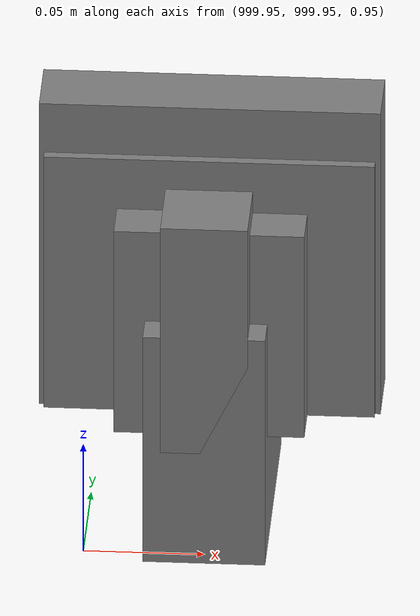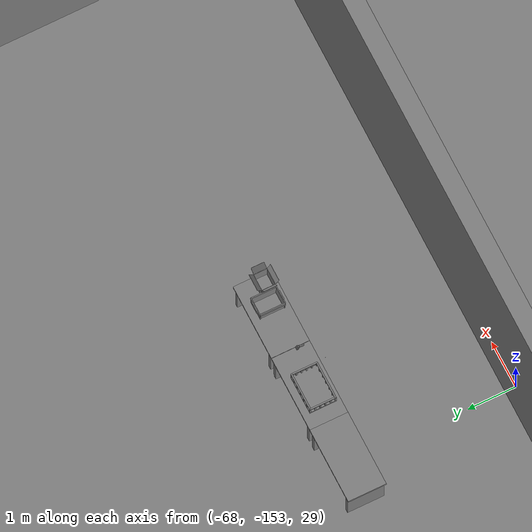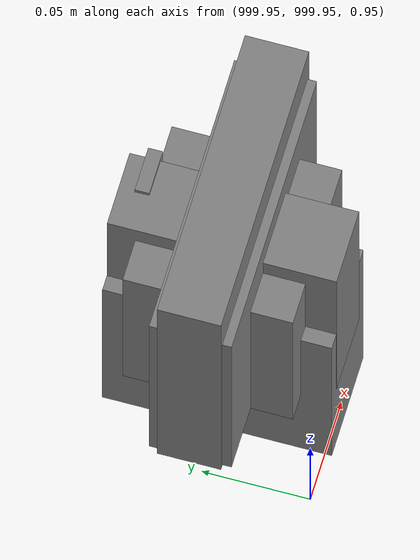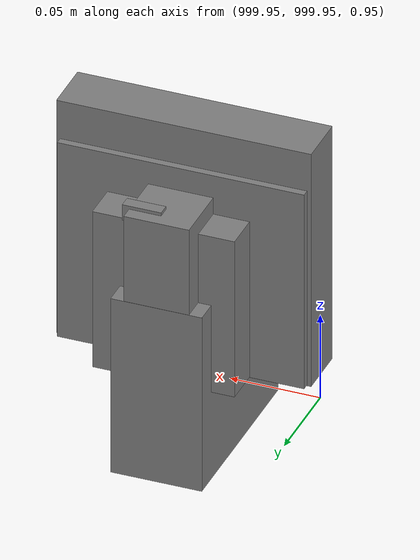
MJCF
<mujoco>
    <option gravity="0.000000000 0.000000000 -9.810000420" timestep="0.0049999999" integrator="implicitfast" density="1.225" viscosity="1.8000001e-05" noslip_iterations="10" iterations="100" sdf_iterations="50">
        <flag multiccd="disable"/>
    </option>
    <size memory="1000M"/>
    <compiler coordinate="local"/>
    <worldbody>
        <light cutoff="30" pos="0 1 1" dir="0 -1 -2"/>
        <light cutoff="30" pos="0 -1 1" dir="0 1 -2"/>
        <body pos="1000.000000000 1000.000000000 1.000000000" euler="0.000000000 0.000000000 180.000000000" name="openloong_gripper_2f85_fix_base_usda_cpu_fan">
            <geom contype="1" conaffinity="1" density="1000" type="box" material="" rgba="0.500000000 0.500000000 0.500000000 1.000000000" solimp="0.899999976 0.949999988 0.001000000" friction="1.000000000 0.005000000 0.000100000" solref="0.020000000 1.000000000" margin="0" condim="3" group="0" pos="0.000000000 0.000000000 0.070034981" quat="0.000000000 0.000000000 0.000000000 1.000000000" size="0.070700005 0.014699999 0.070700005" name="openloong_gripper_2f85_fix_base_usda_geom_734562B8_1CDB_4C23_80D8_C55B50CE7E51"/>
            <freejoint name="openloong_gripper_2f85_fix_base_usda_cpu_fan_joint"/>
            <site size="0.005000000 0.005000000 0.005000000" rgba="0.500000000 0.500000000 0.500000000 1.000000000" pos="0.000000000 0.000000000 0.000000000" quat="0.999961913 0.008726535 0.000000000 0.000000000" group="0" type="sphere" name="openloong_gripper_2f85_fix_base_usda_cpu_fancsite"/>
        </body>
        <body pos="-66.322074890 -149.413940430 31.163633347" euler="-98.901985168 -34.102039337 10.094217300" mocap="true" name="spotlight5_SpotLight"/>
        <body pos="1000.000000000 999.999938965 1.000000000" euler="0.000000000 0.000000000 180.000000000" name="openloong_gripper_2f85_fix_base_usda_intelcore_i5">
            <geom contype="1" conaffinity="1" density="1000" type="box" material="" rgba="0.500000000 0.500000000 0.500000000 1.000000000" solimp="0.899999976 0.949999988 0.001000000" friction="1.000000000 0.005000000 0.000100000" solref="0.020000000 1.000000000" margin="0" condim="3" group="0" pos="0.000000000 0.000000000 0.051722717" quat="0.707106709 0.000000000 0.000000000 -0.707106769" size="0.052800000 0.018080002 0.052800000" name="openloong_gripper_2f85_fix_base_usda_geom_59F1C608_60E0_45E0_86AE_DD2BB9E41B2C"/>
            <freejoint name="openloong_gripper_2f85_fix_base_usda_intelcore_i5_joint"/>
            <site size="0.005000000 0.005000000 0.005000000" rgba="0.500000000 0.500000000 0.500000000 1.000000000" pos="0.000000000 0.000000000 0.000000000" quat="0.999961913 0.008726534 0.000000000 0.000000000" group="0" type="sphere" name="openloong_gripper_2f85_fix_base_usda_intelcore_i5site"/>
        </body>
        <body pos="1000.000000000 1000.000000000 1.000000000" euler="0.000011953 0.000005123 -179.999984741" name="openloong_gripper_2f85_fix_base_usda_intel_box">
            <geom contype="1" conaffinity="1" density="1000" type="box" material="" rgba="0.500000000 0.500000000 0.500000000 1.000000000" solimp="0.899999976 0.949999988 0.001000000" friction="1.000000000 0.005000000 0.000100000" solref="0.020000000 1.000000000" margin="0" condim="3" group="0" pos="0.000000000 -0.000067139 0.000082284" quat="0.707106709 0.000000225 0.000000253 0.707106650" size="0.052800003 0.025300000 0.052800003" name="openloong_gripper_2f85_fix_base_usda_geom_DB704514_CA24_4BB3_9F83_FF99E2453BB3"/>
            <freejoint name="openloong_gripper_2f85_fix_base_usda_intel_box_joint"/>
            <site size="0.005000000 0.005000000 0.005000000" rgba="0.500000000 0.500000000 0.500000000 1.000000000" pos="0.000000000 0.000000000 0.000000000" quat="0.999961913 0.008726500 0.000000000 0.000000000" group="0" type="sphere" name="openloong_gripper_2f85_fix_base_usda_intel_boxsite"/>
        </body>
        <body pos="1000.000000000 1000.000000000 1.000000000" euler="0.000000000 0.000000000 180.000000000" name="openloong_gripper_2f85_fix_base_usda_wifi_box">
            <geom contype="1" conaffinity="1" density="1000" type="box" material="" rgba="0.500000000 0.500000000 0.500000000 1.000000000" solimp="0.899999976 0.949999988 0.001000000" friction="1.000000000 0.005000000 0.000100000" solref="0.020000000 1.000000000" margin="0" condim="3" group="0" pos="0.000000000 0.000000000 0.058978677" quat="0.000000000 0.000000047 0.000000000 1.000000000" size="0.068499997 0.018999999 0.059000000" name="openloong_gripper_2f85_fix_base_usda_geom_387782AB_372E_477B_A750_7B370F083870"/>
            <freejoint name="openloong_gripper_2f85_fix_base_usda_wifi_box_joint"/>
            <site size="0.005000000 0.005000000 0.005000000" rgba="0.500000000 0.500000000 0.500000000 1.000000000" pos="0.000000000 0.000000000 0.000000000" quat="0.999961913 0.008726500 0.000000000 0.000000000" group="0" type="sphere" name="openloong_gripper_2f85_fix_base_usda_wifi_boxsite"/>
        </body>
        <body pos="-66.002059937 -149.313888550 31.171628952" euler="34.022949219 -60.512500763 -49.154800415" mocap="true" name="spotlight3_SpotLight"/>
        <body pos="1000.000000000 1000.000000000 1.000000000" euler="0.000000000 0.000000000 180.000000000" name="openloong_gripper_2f85_fix_base_usda_battery_01">
            <geom contype="1" conaffinity="1" density="1000" type="box" material="" rgba="0.500000000 0.500000000 0.500000000 1.000000000" solimp="0.899999976 0.949999988 0.001000000" friction="1.000000000 0.005000000 0.000100000" solref="0.020000000 1.000000000" margin="0" condim="3" group="0" pos="-0.011123657 -0.041940309 0.101691343" quat="1.000000000 0.000000000 0.000000000 0.000000000" size="0.010800000 0.003375000 0.004725000" name="openloong_gripper_2f85_fix_base_usda_geom_BD21F07C_F330_4833_A9BA_980848E17CB0"/>
            <geom contype="1" conaffinity="1" density="1000" type="box" material="" rgba="0.500000000 0.500000000 0.500000000 1.000000000" solimp="0.899999976 0.949999988 0.001000000" friction="1.000000000 0.005000000 0.000100000" solref="0.020000000 1.000000000" margin="0" condim="3" group="0" pos="-0.010876465 -0.044247437 0.047066893" quat="0.998702705 -0.050920475 0.000000000 0.000000000" size="0.009450001 0.002700000 0.024975000" name="openloong_gripper_2f85_fix_base_usda_geom_D2077C25_C651_4948_A2C1_EAF4F04F0BEF"/>
            <geom contype="1" conaffinity="1" density="1000" type="box" material="" rgba="0.500000000 0.500000000 0.500000000 1.000000000" solimp="0.899999976 0.949999988 0.001000000" friction="1.000000000 0.005000000 0.000100000" solref="0.020000000 1.000000000" margin="0" condim="3" group="0" pos="-0.001235962 -0.000659180 0.047381196" quat="1.000000000 0.000000000 0.000000000 0.000000000" size="0.039420001 0.039150000 0.047250003" name="openloong_gripper_2f85_fix_base_usda_geom_8E34827E_7601_44B1_9C0C_90C50B8FBBE9"/>
            <geom contype="1" conaffinity="1" density="1000" type="box" material="" rgba="0.500000000 0.500000000 0.500000000 1.000000000" solimp="0.899999976 0.949999988 0.001000000" friction="1.000000000 0.005000000 0.000100000" solref="0.020000000 1.000000000" margin="0" condim="3" group="0" pos="-0.010876465 -0.039138794 0.009851727" quat="1.000000000 0.000000000 0.000000000 0.000000000" size="0.009450001 0.010800000 0.013500000" name="openloong_gripper_2f85_fix_base_usda_geom_11D423A2_D393_495D_A372_B4DFAA2F5A4E"/>
            <geom contype="1" conaffinity="1" density="1000" type="box" material="" rgba="0.500000000 0.500000000 0.500000000 1.000000000" solimp="0.899999976 0.949999988 0.001000000" friction="1.000000000 0.005000000 0.000100000" solref="0.020000000 1.000000000" margin="0" condim="3" group="0" pos="-0.010876465 -0.041528322 0.071508206" quat="1.000000000 0.000000000 0.000000000 0.000000000" size="0.009450001 0.002700000 0.027000001" name="openloong_gripper_2f85_fix_base_usda_geom_A5E3837A_8F86_4F47_8E25_DF6008C8651A"/>
            <freejoint name="openloong_gripper_2f85_fix_base_usda_battery_01_joint"/>
            <site size="0.005000000 0.005000000 0.005000000" rgba="0.500000000 0.500000000 0.500000000 1.000000000" pos="0.000000000 0.000000000 0.000000000" quat="0.999961913 0.008726500 0.000000000 0.000000000" group="0" type="sphere" name="openloong_gripper_2f85_fix_base_usda_battery_01site"/>
        </body>
        <body pos="-66.024734497 -148.913986206 31.170135498" euler="-14.872630119 60.042640686 -116.925918579" mocap="true" name="spotlight4_SpotLight"/>
        <body pos="-64.866622925 -149.383972168 30.183746338" euler="89.999984741 89.999946594 0.000000000" name="openloong_gripper_2f85_fix_base_usda_bluebox_01">
            <geom contype="1" conaffinity="1" density="1000" type="box" material="" rgba="0.500000000 0.500000000 0.500000000 1.000000000" solimp="0.899999976 0.949999988 0.001000000" friction="1.000000000 0.005000000 0.000100000" solref="0.020000000 1.000000000" margin="0" condim="3" group="0" pos="0.276580811 0.187225342 0.000068665" quat="0.707106948 0.000077471 0.707106352 0.000077486" size="0.100000001 0.057999998 0.010000000" name="openloong_gripper_2f85_fix_base_usda_geom_96AD08F8_4C6E_468C_9828_B6B1A17F58D4"/>
            <geom contype="1" conaffinity="1" density="1000" type="box" material="" rgba="0.500000000 0.500000000 0.500000000 1.000000000" solimp="0.899999976 0.949999988 0.001000000" friction="1.000000000 0.005000000 0.000100000" solref="0.020000000 1.000000000" margin="0" condim="3" group="0" pos="0.000000000 0.002883911 0.000000000" quat="0.999999881 0.000000000 0.000000000 0.000000000" size="0.254000008 0.003000000 0.172000006" name="openloong_gripper_2f85_fix_base_usda_geom_AA5CCEB0_55A9_4BF2_A5EF_F21D2348C6AC"/>
            <geom contype="1" conaffinity="1" density="1000" type="box" material="" rgba="0.500000000 0.500000000 0.500000000 1.000000000" solimp="0.899999976 0.949999988 0.001000000" friction="1.000000000 0.005000000 0.000100000" solref="0.020000000 1.000000000" margin="0" condim="3" group="0" pos="0.000000000 0.124874115 0.173484802" quat="0.999796331 0.020176515 -0.000000015 0.000000030" size="0.259999990 0.119999997 0.007000000" name="openloong_gripper_2f85_fix_base_usda_geom_91E173F9_C4B3_4BA2_A09E_50337E60E9A6"/>
            <geom contype="1" conaffinity="1" density="1000" type="box" material="" rgba="0.500000000 0.500000000 0.500000000 1.000000000" solimp="0.899999976 0.949999988 0.001000000" friction="1.000000000 0.005000000 0.000100000" solref="0.020000000 1.000000000" margin="0" condim="3" group="0" pos="0.000000000 0.124874115 -0.173469543" quat="0.999796331 -0.020176545 -0.000000015 0.000000000" size="0.259999990 0.119999997 0.007000000" name="openloong_gripper_2f85_fix_base_usda_geom_73BA2E66_E664_415B_99A9_8DEEF147C546"/>
            <geom contype="1" conaffinity="1" density="1000" type="box" material="" rgba="0.500000000 0.500000000 0.500000000 1.000000000" solimp="0.899999976 0.949999988 0.001000000" friction="1.000000000 0.005000000 0.000100000" solref="0.020000000 1.000000000" margin="0" condim="3" group="0" pos="0.000000000 0.214008331 0.188980103" quat="0.999912977 0.013176724 0.000000015 0.000000000" size="0.259999990 0.029999999 0.012500000" name="openloong_gripper_2f85_fix_base_usda_geom_521CCE80_35E2_443A_9D29_86AE5B84F514"/>
            <geom contype="1" conaffinity="1" density="1000" type="box" material="" rgba="0.500000000 0.500000000 0.500000000 1.000000000" solimp="0.899999976 0.949999988 0.001000000" friction="1.000000000 0.005000000 0.000100000" solref="0.020000000 1.000000000" margin="0" condim="3" group="0" pos="-0.258361816 0.125289917 0.001876831" quat="0.702796936 -0.020792112 0.710783124 0.020769298" size="0.189999998 0.119999997 0.009000000" name="openloong_gripper_2f85_fix_base_usda_geom_818BC29D_7B8E_4579_BFCD_09D331B849B2"/>
            <geom contype="1" conaffinity="1" density="1000" type="box" material="" rgba="0.500000000 0.500000000 0.500000000 1.000000000" solimp="0.899999976 0.949999988 0.001000000" friction="1.000000000 0.005000000 0.000100000" solref="0.020000000 1.000000000" margin="0" condim="3" group="0" pos="0.000000000 0.214008331 -0.188980103" quat="0.999912977 -0.013176769 0.000000030 0.000000015" size="0.259999990 0.029999999 0.012500000" name="openloong_gripper_2f85_fix_base_usda_geom_4AE4F4D7_2B8F_44E9_A269_E071F68E263C"/>
            <geom contype="1" conaffinity="1" density="1000" type="box" material="" rgba="0.500000000 0.500000000 0.500000000 1.000000000" solimp="0.899999976 0.949999988 0.001000000" friction="1.000000000 0.005000000 0.000100000" solref="0.020000000 1.000000000" margin="0" condim="3" group="0" pos="-0.276611328 0.187225342 0.000068665" quat="0.707106650 0.000077441 0.707106709 0.000077456" size="0.100000001 0.057999998 0.010000000" name="openloong_gripper_2f85_fix_base_usda_geom_58FBCBF1_9B04_42A2_BE6B_26F091FD1182"/>
            <geom contype="1" conaffinity="1" density="1000" type="box" material="" rgba="0.500000000 0.500000000 0.500000000 1.000000000" solimp="0.899999976 0.949999988 0.001000000" friction="1.000000000 0.005000000 0.000100000" solref="0.020000000 1.000000000" margin="0" condim="3" group="0" pos="0.258331299 0.125289917 0.001876831" quat="0.702851415 0.018856421 0.710823774 -0.019329369" size="0.189999998 0.119999997 0.009000000" name="openloong_gripper_2f85_fix_base_usda_geom_6D757CD4_A42A_4ED2_8631_75B2A3E89689"/>
            <freejoint name="openloong_gripper_2f85_fix_base_usda_bluebox_01_joint"/>
            <site size="0.005000000 0.005000000 0.005000000" rgba="0.500000000 0.500000000 0.500000000 1.000000000" pos="0.000000000 0.000000000 0.000000000" quat="0.999961913 0.008726534 0.000000000 0.000000000" group="0" type="sphere" name="openloong_gripper_2f85_fix_base_usda_bluebox_01site"/>
        </body>
        <body pos="-64.496299744 -149.491867065 30.235729218" euler="0.000000000 0.000000000 89.999946594" name="openloong_gripper_2f85_fix_base_usda_cardboardbox_01">
            <geom contype="1" conaffinity="1" density="1000" type="box" material="" rgba="0.500000000 0.500000000 0.500000000 1.000000000" solimp="0.899999976 0.949999988 0.001000000" friction="1.000000000 0.005000000 0.000100000" solref="0.020000000 1.000000000" margin="0" condim="3" group="0" pos="-0.003166199 -0.004086494 0.005052090" quat="1.000000000 0.000000000 0.000000000 0.000000000" size="0.142499998 0.177500010 0.005000000" name="openloong_gripper_2f85_fix_base_usda_geom_FF08E902_3156_44DB_A442_2709C8E16257"/>
            <geom contype="1" conaffinity="1" density="1000" type="box" material="" rgba="0.500000000 0.500000000 0.500000000 1.000000000" solimp="0.899999976 0.949999988 0.001000000" friction="1.000000000 0.005000000 0.000100000" solref="0.020000000 1.000000000" margin="0" condim="3" group="0" pos="-0.003166199 0.170316696 0.150570869" quat="1.000000000 0.000000000 0.000000000 0.000000000" size="0.142499998 0.005000000 0.149999991" name="openloong_gripper_2f85_fix_base_usda_geom_F5DF3E88_DD9F_4F52_B460_F1AB0E82F56A"/>
            <geom contype="1" conaffinity="1" density="1000" type="box" material="" rgba="0.500000000 0.500000000 0.500000000 1.000000000" solimp="0.899999976 0.949999988 0.001000000" friction="1.000000000 0.005000000 0.000100000" solref="0.020000000 1.000000000" margin="0" condim="3" group="0" pos="-0.147399902 -0.005307198 0.150570869" quat="1.000000000 0.000000000 0.000000000 0.000000000" size="0.005000000 0.177500010 0.149999991" name="openloong_gripper_2f85_fix_base_usda_geom_BA1E4972_683E_4623_ABBE_AC257084763F"/>
            <geom contype="1" conaffinity="1" density="1000" type="box" material="" rgba="0.500000000 0.500000000 0.500000000 1.000000000" solimp="0.899999976 0.949999988 0.001000000" friction="1.000000000 0.005000000 0.000100000" solref="0.020000000 1.000000000" margin="0" condim="3" group="0" pos="0.140275955 -0.005307198 0.150570869" quat="1.000000000 0.000000000 0.000000000 0.000000000" size="0.005000000 0.177500010 0.149999991" name="openloong_gripper_2f85_fix_base_usda_geom_386EE11A_0A55_4A61_B1AB_3B2E9864F78C"/>
            <geom contype="1" conaffinity="1" density="1000" type="box" material="" rgba="0.500000000 0.500000000 0.500000000 1.000000000" solimp="0.899999976 0.949999988 0.001000000" friction="1.000000000 0.005000000 0.000100000" solref="0.020000000 1.000000000" margin="0" condim="3" group="0" pos="-0.003166199 -0.181550980 0.150570869" quat="1.000000000 0.000000000 0.000000000 0.000000000" size="0.142499998 0.005000000 0.149999991" name="openloong_gripper_2f85_fix_base_usda_geom_B68FD1EC_AEBB_4126_A3CF_B22144D917AA"/>
            <freejoint name="openloong_gripper_2f85_fix_base_usda_cardboardbox_01_joint"/>
            <site size="0.005000000 0.005000000 0.005000000" rgba="0.500000000 0.500000000 0.500000000 1.000000000" pos="0.000000000 0.000000000 0.000000000" quat="0.999961913 0.008726535 0.000000000 0.000000000" group="0" type="sphere" name="openloong_gripper_2f85_fix_base_usda_site_D5760F40_4E48_45DA_B59F_D7E236BF5F9D"/>
            <body pos="0.139160156 -0.004048347 0.301930904" euler="-179.999954224 49.383502960 179.999954224" name="openloong_gripper_2f85_fix_base_usda_A1_006">
                <geom contype="1" conaffinity="1" density="1000" type="box" material="" rgba="0.500000000 0.500000000 0.500000000 1.000000000" solimp="0.899999976 0.949999988 0.001000000" friction="1.000000000 0.005000000 0.000100000" solref="0.020000000 1.000000000" margin="0" condim="3" group="0" pos="-0.071587563 0.000009537 0.001745224" quat="0.999999881 0.000000000 0.000000000 0.000000000" size="0.071249999 0.179999992 0.002500000" name="openloong_gripper_2f85_fix_base_usda_geom_6AAA9448_14A0_4DDD_A04A_1A16AEDC4AC4"/>
                <joint armature="0" stiffness="0.07" damping="0.0099999998" axis="0.000000 1.000000 0.000000" type="hinge" name="openloong_gripper_2f85_fix_base_usda_A1_006"/>
            </body>
            <body pos="-0.145902634 -0.004086494 0.301938057" euler="-180.000000000 -60.000011444 -180.000000000" name="openloong_gripper_2f85_fix_base_usda_A2_006">
                <geom contype="1" conaffinity="1" density="1000" type="box" material="" rgba="0.500000000 0.500000000 0.500000000 1.000000000" solimp="0.899999976 0.949999988 0.001000000" friction="1.000000000 0.005000000 0.000100000" solref="0.020000000 1.000000000" margin="0" condim="3" group="0" pos="0.071268082 0.000009537 0.002717972" quat="0.000002921 0.000000000 -0.000000030 0.999999881" size="0.071249999 0.179999992 0.002500000" name="openloong_gripper_2f85_fix_base_usda_geom_F466DBDC_B390_4697_BBEC_FC42C3DD8DB9"/>
                <joint armature="0" stiffness="0.07" damping="0.0099999998" axis="0.000000 1.000000 0.000000" type="hinge" name="openloong_gripper_2f85_fix_base_usda_A2_006"/>
            </body>
            <body pos="-0.003385544 0.175991058 0.301930904" euler="-125.858116150 -0.000004561 0.000002331" name="openloong_gripper_2f85_fix_base_usda_B2_006">
                <geom contype="1" conaffinity="1" density="1000" type="box" material="" rgba="0.500000000 0.500000000 0.500000000 1.000000000" solimp="0.899999976 0.949999988 0.001000000" friction="1.000000000 0.005000000 0.000100000" solref="0.020000000 1.000000000" margin="0" condim="3" group="0" pos="0.000009537 -0.070939064 -0.002470016" quat="0.999614120 0.027776197 -0.000000015 0.000000030" size="0.137500003 0.064999998 0.005000000" name="openloong_gripper_2f85_fix_base_usda_geom_7578A776_54FA_4563_90FE_4D583FBC5F7B"/>
                <joint armature="0" stiffness="0.07" damping="0.0099999998" axis="1.000000 0.000000 0.000000" type="hinge" name="openloong_gripper_2f85_fix_base_usda_B2_006"/>
            </body>
            <body pos="-0.003385544 -0.184140205 0.301938057" euler="147.805557251 0.000000000 0.000000000" name="openloong_gripper_2f85_fix_base_usda_B1_006">
                <geom contype="1" conaffinity="1" density="1000" type="box" material="" rgba="0.500000000 0.500000000 0.500000000 1.000000000" solimp="0.899999976 0.949999988 0.001000000" friction="1.000000000 0.005000000 0.000100000" solref="0.020000000 1.000000000" margin="0" condim="3" group="0" pos="-0.000028610 0.070202351 -0.002703667" quat="0.999614179 -0.027776167 0.000000000 0.000000000" size="0.137500003 0.064999998 0.005000000" name="openloong_gripper_2f85_fix_base_usda_geom_3D102067_099D_443B_8F0F_9F180C21DDEA"/>
                <joint armature="0" stiffness="0.07" damping="0.0099999998" axis="1.000000 0.000000 0.000000" type="hinge" name="openloong_gripper_2f85_fix_base_usda_B1_006"/>
            </body>
        </body>
        <body pos="-65.882858276 -149.481979370 30.229999542" euler="-64.487716675 0.000000000 0.000000000" name="openloong_gripper_2f85_fix_base_usda_Barcode">
            <geom contype="1" conaffinity="1" density="1000" type="box" material="" rgba="0.500000000 0.500000000 0.500000000 1.000000000" solimp="0.899999976 0.949999988 0.001000000" friction="1.000000000 0.005000000 0.000100000" solref="0.020000000 1.000000000" margin="0" condim="3" group="0" pos="0.000000000 0.013038635 0.001419067" quat="0.000000000 0.000000000 0.000000000 1.000000119" size="0.034000002 0.010000000 0.017999999" name="openloong_gripper_2f85_fix_base_usda_geom_D13DDB82_F606_489E_B373_48953C5F347D"/>
            <geom contype="1" conaffinity="1" density="1000" type="box" material="" rgba="0.500000000 0.500000000 0.500000000 1.000000000" solimp="0.899999976 0.949999988 0.001000000" friction="1.000000000 0.005000000 0.000100000" solref="0.020000000 1.000000000" margin="0" condim="3" group="0" pos="0.000000000 -0.035301208 -0.007095337" quat="0.000000000 0.000000000 -0.043619365 0.999048233" size="0.028999999 0.010000000 0.020000000" name="openloong_gripper_2f85_fix_base_usda_geom_2BE4247C_F07D_4B14_B4C0_5263865F2031"/>
            <geom contype="1" conaffinity="1" density="1000" type="box" material="" rgba="0.500000000 0.500000000 0.500000000 1.000000000" solimp="0.899999976 0.949999988 0.001000000" friction="1.000000000 0.005000000 0.000100000" solref="0.020000000 1.000000000" margin="0" condim="3" group="0" pos="0.000000000 -0.043411255 -0.011749268" quat="0.922262907 0.386563420 0.000000000 0.000000000" size="0.026000001 0.010000000 0.020000000" name="openloong_gripper_2f85_fix_base_usda_geom_6D4115FE_0197_4654_9A1A_48737ABFEA43"/>
            <geom contype="1" conaffinity="1" density="1000" type="box" material="" rgba="0.500000000 0.500000000 0.500000000 1.000000000" solimp="0.899999976 0.949999988 0.001000000" friction="1.000000000 0.005000000 0.000100000" solref="0.020000000 1.000000000" margin="0" condim="3" group="0" pos="0.000000000 -0.016967773 -0.031860352" quat="0.000000000 0.000000000 0.000000000 1.000000119" size="0.008000000 0.010000000 0.013000000" name="openloong_gripper_2f85_fix_base_usda_geom_4163A0DB_1847_43B3_9F4F_A1DDBAE3F149"/>
            <geom contype="1" conaffinity="1" density="1000" type="box" material="" rgba="0.500000000 0.500000000 0.500000000 1.000000000" solimp="0.899999976 0.949999988 0.001000000" friction="1.000000000 0.005000000 0.000100000" solref="0.020000000 1.000000000" margin="0" condim="3" group="0" pos="0.000000000 -0.001869202 0.000312805" quat="0.953716993 0.300705761 0.000000000 0.000000000" size="0.032000002 0.010000000 0.018999999" name="openloong_gripper_2f85_fix_base_usda_geom_F5CB7F59_3C2D_4BD8_8577_114EBA85A21E"/>
            <geom contype="1" conaffinity="1" density="1000" type="box" material="" rgba="0.500000000 0.500000000 0.500000000 1.000000000" solimp="0.899999976 0.949999988 0.001000000" friction="1.000000000 0.005000000 0.000100000" solref="0.020000000 1.000000000" margin="0" condim="3" group="0" pos="0.000000000 -0.019531250 -0.003173828" quat="0.953716993 0.300705761 0.000000000 0.000000000" size="0.030999999 0.010000000 0.020000000" name="openloong_gripper_2f85_fix_base_usda_geom_045CAD64_E0DA_4479_8126_DC8F8B9A8CF6"/>
            <geom contype="1" conaffinity="1" density="1000" type="box" material="" rgba="0.500000000 0.500000000 0.500000000 1.000000000" solimp="0.899999976 0.949999988 0.001000000" friction="1.000000000 0.005000000 0.000100000" solref="0.020000000 1.000000000" margin="0" condim="3" group="0" pos="0.000000000 -0.035301208 -0.007095337" quat="0.953716993 0.300705761 0.000000000 0.000000000" size="0.028999999 0.010000000 0.020000000" name="openloong_gripper_2f85_fix_base_usda_geom_75D8C391_92B4_44B0_82FE_78E7D33C8B6A"/>
            <geom contype="1" conaffinity="1" density="1000" type="box" material="" rgba="0.500000000 0.500000000 0.500000000 1.000000000" solimp="0.899999976 0.949999988 0.001000000" friction="1.000000000 0.005000000 0.000100000" solref="0.020000000 1.000000000" margin="0" condim="3" group="0" pos="0.000000000 -0.042617798 -0.071121216" quat="0.000000000 0.000000000 0.000000000 1.000000119" size="0.013000000 0.021000000 0.059999999" name="openloong_gripper_2f85_fix_base_usda_geom_1DFDE436_DFE4_4025_8D04_244E796676A4"/>
            <freejoint name="openloong_gripper_2f85_fix_base_usda_Barcode_joint"/>
            <site size="0.005000000 0.005000000 0.005000000" rgba="0.500000000 0.500000000 0.500000000 1.000000000" pos="0.000000000 0.000000000 0.000000000" quat="1.000000000 0.000000000 0.000000000 0.000000000" group="0" type="sphere" name="openloong_gripper_2f85_fix_base_usda_Barcode_site"/>
        </body>
        <body pos="-66.745018005 -149.392349243 30.184000015" euler="0.000000000 0.000000000 89.999946594" name="[22329839416566]_Basket_01">
            <geom contype="1" conaffinity="1" density="1000" type="box" material="" rgba="0.500000000 0.500000000 0.500000000 1.000000000" solimp="0.899999976 0.949999988 0.001000000" friction="1.000000000 0.005000000 0.000100000" solref="0.020000000 1.000000000" margin="0" condim="3" group="0" pos="-0.052425385 0.389207840 0.089787483" quat="0.707107008 0.000000000 0.000000000 0.707106411" size="0.014249999 0.014249999 0.059999999" name="[22329839416566]_geom_8AE9001F_51C5_4230_BCDF_6CA87724E4BB"/>
            <geom contype="1" conaffinity="1" density="1000" type="box" material="" rgba="0.500000000 0.500000000 0.500000000 1.000000000" solimp="0.899999976 0.949999988 0.001000000" friction="1.000000000 0.005000000 0.000100000" solref="0.020000000 1.000000000" margin="0" condim="3" group="0" pos="0.264015198 -0.133043289 0.089787483" quat="0.707107008 0.000000000 0.000000000 0.707106411" size="0.014249999 0.014249999 0.059999999" name="[22329839416566]_geom_ADC9B9A3_BF25_45FE_97A0_FFA8DF53E0BE"/>
            <geom contype="1" conaffinity="1" density="1000" type="box" material="" rgba="0.500000000 0.500000000 0.500000000 1.000000000" solimp="0.899999976 0.949999988 0.001000000" friction="1.000000000 0.005000000 0.000100000" solref="0.020000000 1.000000000" margin="0" condim="3" group="0" pos="-0.264015198 -0.265548706 0.089793205" quat="0.707107008 0.000000000 0.000000000 0.707106411" size="0.014249999 0.014249999 0.059999999" name="[22329839416566]_geom_77D4ABCA_1AA8_493B_BA10_E9BDA824AFC7"/>
            <geom contype="1" conaffinity="1" density="1000" type="box" material="" rgba="0.500000000 0.500000000 0.500000000 1.000000000" solimp="0.899999976 0.949999988 0.001000000" friction="1.000000000 0.005000000 0.000100000" solref="0.020000000 1.000000000" margin="0" condim="3" group="0" pos="-0.160263062 -0.389322281 0.089793205" quat="0.707107008 0.000000000 0.000000000 0.707106411" size="0.014249999 0.014249999 0.059999999" name="[22329839416566]_geom_26416EC6_048E_4234_8C1B_14E5CC643BB8"/>
            <geom contype="1" conaffinity="1" density="1000" type="box" material="" rgba="0.500000000 0.500000000 0.500000000 1.000000000" solimp="0.899999976 0.949999988 0.001000000" friction="1.000000000 0.005000000 0.000100000" solref="0.020000000 1.000000000" margin="0" condim="3" group="0" pos="0.162265778 -0.389322281 0.089787483" quat="0.707107008 0.000000000 0.000000000 0.707106411" size="0.014249999 0.014249999 0.059999999" name="[22329839416566]_geom_D9B6859A_4AAF_407A_A939_A150E3E79AF1"/>
            <geom contype="1" conaffinity="1" density="1000" type="box" material="" rgba="0.500000000 0.500000000 0.500000000 1.000000000" solimp="0.899999976 0.949999988 0.001000000" friction="1.000000000 0.005000000 0.000100000" solref="0.020000000 1.000000000" margin="0" condim="3" group="0" pos="0.264015198 0.389207840 0.089787483" quat="0.707107008 0.000000000 0.000000000 0.707106411" size="0.014249999 0.014249999 0.059999999" name="[22329839416566]_geom_00319CE0_51A4_4F03_98FD_DDB44A47013F"/>
            <geom contype="1" conaffinity="1" density="1000" type="box" material="" rgba="0.500000000 0.500000000 0.500000000 1.000000000" solimp="0.899999976 0.949999988 0.001000000" friction="1.000000000 0.005000000 0.000100000" solref="0.020000000 1.000000000" margin="0" condim="3" group="0" pos="-0.264015198 -0.133043289 0.089793205" quat="0.707107008 0.000000000 0.000000000 0.707106411" size="0.014249999 0.014249999 0.059999999" name="[22329839416566]_geom_7C75C35D_4FC4_44EB_B474_7671412035C8"/>
            <geom contype="1" conaffinity="1" density="1000" type="box" material="" rgba="0.500000000 0.500000000 0.500000000 1.000000000" solimp="0.899999976 0.949999988 0.001000000" friction="1.000000000 0.005000000 0.000100000" solref="0.020000000 1.000000000" margin="0" condim="3" group="0" pos="-0.264026642 0.269256592 0.089793205" quat="0.707107008 0.000000000 0.000000000 0.707106411" size="0.014249999 0.014249999 0.059999999" name="[22329839416566]_geom_4D2A8620_B3FF_4526_831A_9C963FB10B40"/>
            <geom contype="1" conaffinity="1" density="1000" type="box" material="" rgba="0.500000000 0.500000000 0.500000000 1.000000000" solimp="0.899999976 0.949999988 0.001000000" friction="1.000000000 0.005000000 0.000100000" solref="0.020000000 1.000000000" margin="0" condim="3" group="0" pos="0.054462433 0.389207840 0.089787483" quat="0.707107008 0.000000000 0.000000000 0.707106411" size="0.014249999 0.014249999 0.059999999" name="[22329839416566]_geom_65AAB845_211E_483F_A2F7_5522CA3CD0C0"/>
            <geom contype="1" conaffinity="1" density="1000" type="box" material="" rgba="0.500000000 0.500000000 0.500000000 1.000000000" solimp="0.899999976 0.949999988 0.001000000" friction="1.000000000 0.005000000 0.000100000" solref="0.020000000 1.000000000" margin="0" condim="3" group="0" pos="0.054462433 -0.389322281 0.089787483" quat="0.707107008 0.000000000 0.000000000 0.707106411" size="0.014249999 0.014249999 0.059999999" name="[22329839416566]_geom_B09C6DDD_6740_4A4D_83D1_60E263131D9E"/>
            <geom contype="1" conaffinity="1" density="1000" type="box" material="" rgba="0.500000000 0.500000000 0.500000000 1.000000000" solimp="0.899999976 0.949999988 0.001000000" friction="1.000000000 0.005000000 0.000100000" solref="0.020000000 1.000000000" margin="0" condim="3" group="0" pos="0.264015198 0.269256592 0.089793205" quat="0.707107008 0.000000000 0.000000000 0.707106411" size="0.014249999 0.014249999 0.059999999" name="[22329839416566]_geom_6FA79665_A4EC_4A2B_95F7_F2D270763906"/>
            <geom contype="1" conaffinity="1" density="1000" type="box" material="" rgba="0.500000000 0.500000000 0.500000000 1.000000000" solimp="0.899999976 0.949999988 0.001000000" friction="1.000000000 0.005000000 0.000100000" solref="0.020000000 1.000000000" margin="0" condim="3" group="0" pos="0.264015198 -0.389322281 0.089787483" quat="0.707107008 0.000000000 0.000000000 0.707106411" size="0.014249999 0.014249999 0.059999999" name="[22329839416566]_geom_E457804F_A042_4E9E_BC9A_93A112544F05"/>
            <geom contype="1" conaffinity="1" density="1000" type="box" material="" rgba="0.500000000 0.500000000 0.500000000 1.000000000" solimp="0.899999976 0.949999988 0.001000000" friction="1.000000000 0.005000000 0.000100000" solref="0.020000000 1.000000000" margin="0" condim="3" group="0" pos="0.000000000 0.000000000 0.015998840" quat="0.707107008 0.000000000 0.000000000 0.707106411" size="0.403499991 0.279000014 0.015750000" name="[22329839416566]_geom_D5B78A8D_E293_47C2_844A_4F1B0C1F2D7F"/>
            <geom contype="1" conaffinity="1" density="1000" type="box" material="" rgba="0.500000000 0.500000000 0.500000000 1.000000000" solimp="0.899999976 0.949999988 0.001000000" friction="1.000000000 0.005000000 0.000100000" solref="0.020000000 1.000000000" margin="0" condim="3" group="0" pos="0.000000000 -0.389476776 0.163619041" quat="0.707107008 0.000000000 0.000000000 0.707106411" size="0.015000000 0.277500004 0.015750000" name="[22329839416566]_geom_61061F9D_26A0_4F8E_B585_D5AEE00CCE9A"/>
            <geom contype="1" conaffinity="1" density="1000" type="box" material="" rgba="0.500000000 0.500000000 0.500000000 1.000000000" solimp="0.899999976 0.949999988 0.001000000" friction="1.000000000 0.005000000 0.000100000" solref="0.020000000 1.000000000" margin="0" condim="3" group="0" pos="0.162265778 0.389207840 0.089787483" quat="0.707107008 0.000000000 0.000000000 0.707106411" size="0.014249999 0.014249999 0.059999999" name="[22329839416566]_geom_A6B034B1_7B5B_4866_85C9_8E99EF4BF60E"/>
            <geom contype="1" conaffinity="1" density="1000" type="box" material="" rgba="0.500000000 0.500000000 0.500000000 1.000000000" solimp="0.899999976 0.949999988 0.001000000" friction="1.000000000 0.005000000 0.000100000" solref="0.020000000 1.000000000" margin="0" condim="3" group="0" pos="0.000000000 0.389471054 0.163619041" quat="0.707107008 0.000000000 0.000000000 0.707106411" size="0.015000000 0.277500004 0.015750000" name="[22329839416566]_geom_97D5A0D5_0B72_4334_8265_EB1EDCBD7F8C"/>
            <geom contype="1" conaffinity="1" density="1000" type="box" material="" rgba="0.500000000 0.500000000 0.500000000 1.000000000" solimp="0.899999976 0.949999988 0.001000000" friction="1.000000000 0.005000000 0.000100000" solref="0.020000000 1.000000000" margin="0" condim="3" group="0" pos="-0.263511658 0.000000000 0.163619041" quat="0.707107008 0.000000000 0.000000000 0.707106411" size="0.403499991 0.015000000 0.015750000" name="[22329839416566]_geom_25AC7F89_65C3_41E6_8F87_CC286D72A466"/>
            <geom contype="1" conaffinity="1" density="1000" type="box" material="" rgba="0.500000000 0.500000000 0.500000000 1.000000000" solimp="0.899999976 0.949999988 0.001000000" friction="1.000000000 0.005000000 0.000100000" solref="0.020000000 1.000000000" margin="0" condim="3" group="0" pos="-0.264015198 0.141334534 0.089793205" quat="0.707107008 0.000000000 0.000000000 0.707106411" size="0.014249999 0.014249999 0.059999999" name="[22329839416566]_geom_C1BF3DD3_7FE1_4852_B805_5F8C953B2AD2"/>
            <geom contype="1" conaffinity="1" density="1000" type="box" material="" rgba="0.500000000 0.500000000 0.500000000 1.000000000" solimp="0.899999976 0.949999988 0.001000000" friction="1.000000000 0.005000000 0.000100000" solref="0.020000000 1.000000000" margin="0" condim="3" group="0" pos="0.264015198 -0.265548706 0.089787483" quat="0.707107008 0.000000000 0.000000000 0.707106411" size="0.014249999 0.014249999 0.059999999" name="[22329839416566]_geom_00F45948_9D02_4008_B519_A31ABE74EE85"/>
            <geom contype="1" conaffinity="1" density="1000" type="box" material="" rgba="0.500000000 0.500000000 0.500000000 1.000000000" solimp="0.899999976 0.949999988 0.001000000" friction="1.000000000 0.005000000 0.000100000" solref="0.020000000 1.000000000" margin="0" condim="3" group="0" pos="-0.160263062 0.389207840 0.089787483" quat="0.707107008 0.000000000 0.000000000 0.707106411" size="0.014249999 0.014249999 0.059999999" name="[22329839416566]_geom_70BD854B_91BC_4395_9794_5552952C8857"/>
            <geom contype="1" conaffinity="1" density="1000" type="box" material="" rgba="0.500000000 0.500000000 0.500000000 1.000000000" solimp="0.899999976 0.949999988 0.001000000" friction="1.000000000 0.005000000 0.000100000" solref="0.020000000 1.000000000" margin="0" condim="3" group="0" pos="-0.052425385 -0.389322281 0.089787483" quat="0.707107008 0.000000000 0.000000000 0.707106411" size="0.014249999 0.014249999 0.059999999" name="[22329839416566]_geom_C1B47229_2648_4BC8_BD15_CB47A31BF90F"/>
            <geom contype="1" conaffinity="1" density="1000" type="box" material="" rgba="0.500000000 0.500000000 0.500000000 1.000000000" solimp="0.899999976 0.949999988 0.001000000" friction="1.000000000 0.005000000 0.000100000" solref="0.020000000 1.000000000" margin="0" condim="3" group="0" pos="-0.264026642 -0.389322281 0.089793205" quat="0.707107008 0.000000000 0.000000000 0.707106411" size="0.014249999 0.014249999 0.059999999" name="[22329839416566]_geom_5EECF387_3535_4983_A84F_A966B2E63BDA"/>
            <geom contype="1" conaffinity="1" density="1000" type="box" material="" rgba="0.500000000 0.500000000 0.500000000 1.000000000" solimp="0.899999976 0.949999988 0.001000000" friction="1.000000000 0.005000000 0.000100000" solref="0.020000000 1.000000000" margin="0" condim="3" group="0" pos="0.264015198 0.141334534 0.089787483" quat="0.707107008 0.000000000 0.000000000 0.707106411" size="0.014249999 0.014249999 0.059999999" name="[22329839416566]_geom_90C55B82_E393_4713_A291_11E1D8297B8B"/>
            <geom contype="1" conaffinity="1" density="1000" type="box" material="" rgba="0.500000000 0.500000000 0.500000000 1.000000000" solimp="0.899999976 0.949999988 0.001000000" friction="1.000000000 0.005000000 0.000100000" solref="0.020000000 1.000000000" margin="0" condim="3" group="0" pos="-0.264015198 0.389207840 0.089793205" quat="0.707107008 0.000000000 0.000000000 0.707106411" size="0.014249999 0.014249999 0.059999999" name="[22329839416566]_geom_55CC6938_F1AF_4627_BB9B_7F659D79E7C1"/>
            <geom contype="1" conaffinity="1" density="1000" type="box" material="" rgba="0.500000000 0.500000000 0.500000000 1.000000000" solimp="0.899999976 0.949999988 0.001000000" friction="1.000000000 0.005000000 0.000100000" solref="0.020000000 1.000000000" margin="0" condim="3" group="0" pos="0.264015198 0.004480362 0.089787483" quat="0.707107008 0.000000000 0.000000000 0.707106411" size="0.014249999 0.014249999 0.059999999" name="[22329839416566]_geom_F1D5E0D8_39CB_4335_BEED_BB1287299815"/>
            <geom contype="1" conaffinity="1" density="1000" type="box" material="" rgba="0.500000000 0.500000000 0.500000000 1.000000000" solimp="0.899999976 0.949999988 0.001000000" friction="1.000000000 0.005000000 0.000100000" solref="0.020000000 1.000000000" margin="0" condim="3" group="0" pos="0.263694763 -0.000011444 0.163619041" quat="0.707107008 0.000000000 0.000000000 0.707106411" size="0.403499991 0.015000000 0.015750000" name="[22329839416566]_geom_2A8FBD5E_E51F_4A06_B587_BDD4DEF264FB"/>
            <geom contype="1" conaffinity="1" density="1000" type="box" material="" rgba="0.500000000 0.500000000 0.500000000 1.000000000" solimp="0.899999976 0.949999988 0.001000000" friction="1.000000000 0.005000000 0.000100000" solref="0.020000000 1.000000000" margin="0" condim="3" group="0" pos="-0.264015198 0.004480362 0.089793205" quat="0.707107008 0.000000000 0.000000000 0.707106411" size="0.014249999 0.014249999 0.059999999" name="[22329839416566]_geom_FBF99B43_92D4_4468_AF27_BD38DEC88363"/>
            <freejoint name="[22329839416566]_joint_080E9137_C1BB_4C92_8BC1_D55067F3A889"/>
        </body>
        <body pos="0.000000000 0.000000000 0.000000000" euler="0.000000000 0.000000000 0.000000000" name="Static Objects_Static Objects">
            <geom contype="1" conaffinity="1" density="1000" type="box" material="" rgba="0.500000000 0.500000000 0.500000000 1.000000000" solimp="0.899999976 0.949999988 0.001000000" friction="1.000000000 0.005000000 0.000100000" solref="0.020000000 1.000000000" margin="0" condim="3" group="0" pos="-67.544113159 -149.365814209 29.727830887" quat="0.500000417 0.499999970 0.499999553 0.499999970" size="0.381000012 0.319999993 0.041000001" name="Static Objects_geom_E5686F70_1930_4545_B790_A4EACCB70AA5"/>
            <geom contype="1" conaffinity="1" density="1000" type="box" material="" rgba="0.500000000 0.500000000 0.500000000 1.000000000" solimp="0.899999976 0.949999988 0.001000000" friction="1.000000000 0.005000000 0.000100000" solref="0.020000000 1.000000000" margin="0" condim="3" group="0" pos="-68.239501953 -149.365814209 30.086868286" quat="0.500000417 0.499999970 0.499999553 0.499999970" size="0.370999992 0.039500002 0.745000005" name="Static Objects_geom_4A60C0BB_7594_4D02_8D39_38E9A6B9ACF4"/>
            <geom contype="1" conaffinity="1" density="1000" type="box" material="" rgba="0.500000000 0.500000000 0.500000000 1.000000000" solimp="0.899999976 0.949999988 0.001000000" friction="1.000000000 0.005000000 0.000100000" solref="0.020000000 1.000000000" margin="0" condim="3" group="0" pos="-68.239501953 -149.365814209 30.147235870" quat="0.500000417 0.499999970 0.499999553 0.499999970" size="0.400000006 0.022000000 0.800000012" name="Static Objects_geom_C526BB9C_B74C_4DA8_9E3B_F0B53BB100B4"/>
            <geom contype="1" conaffinity="1" density="1000" type="box" material="" rgba="0.500000000 0.500000000 0.500000000 1.000000000" solimp="0.899999976 0.949999988 0.001000000" friction="1.000000000 0.005000000 0.000100000" solref="0.020000000 1.000000000" margin="0" condim="3" group="0" pos="-68.934890747 -149.365814209 29.727830887" quat="0.500000417 0.499999970 0.499999553 0.499999970" size="0.381000012 0.319999993 0.041000001" name="Static Objects_geom_64FA8BBB_1DD7_4CB6_883D_E06FBAD7C23D"/>
            <geom contype="1" conaffinity="1" density="1000" type="box" material="" rgba="0.500000000 0.500000000 0.500000000 1.000000000" solimp="0.899999976 0.949999988 0.001000000" friction="1.000000000 0.005000000 0.000100000" solref="0.020000000 1.000000000" margin="0" condim="3" group="0" pos="-68.239501953 -149.365814209 29.561563492" quat="0.500000417 0.499999970 0.499999553 0.499999970" size="0.020000000 0.022000000 0.660000026" name="Static Objects_geom_D45491F6_DDEC_4DDC_B5D9_CD9611BC3DA6"/>
            <geom contype="1" conaffinity="1" density="1000" type="box" material="" rgba="0.500000000 0.500000000 0.500000000 1.000000000" solimp="0.899999976 0.949999988 0.001000000" friction="1.000000000 0.005000000 0.000100000" solref="0.020000000 1.000000000" margin="0" condim="3" group="0" pos="-65.945671082 -149.365814209 29.727830887" quat="0.500000417 0.499999970 0.499999553 0.499999970" size="0.381000012 0.319999993 0.041000001" name="Static Objects_geom_7B2F838F_CC71_48E3_B236_8D1ECA1BC48A"/>
            <geom contype="1" conaffinity="1" density="1000" type="box" material="" rgba="0.500000000 0.500000000 0.500000000 1.000000000" solimp="0.899999976 0.949999988 0.001000000" friction="1.000000000 0.005000000 0.000100000" solref="0.020000000 1.000000000" margin="0" condim="3" group="0" pos="-66.641059875 -149.365814209 30.086868286" quat="0.500000417 0.499999970 0.499999553 0.499999970" size="0.370999992 0.039500002 0.745000005" name="Static Objects_geom_2946245B_51C6_470B_952F_AECF8D9F5A07"/>
            <geom contype="1" conaffinity="1" density="1000" type="box" material="" rgba="0.500000000 0.500000000 0.500000000 1.000000000" solimp="0.899999976 0.949999988 0.001000000" friction="1.000000000 0.005000000 0.000100000" solref="0.020000000 1.000000000" margin="0" condim="3" group="0" pos="-66.641059875 -149.365814209 30.147235870" quat="0.500000417 0.499999970 0.499999553 0.499999970" size="0.400000006 0.022000000 0.800000012" name="Static Objects_geom_C8BC2178_360F_400A_8457_6ACE9FA839F2"/>
            <geom contype="1" conaffinity="1" density="1000" type="box" material="" rgba="0.500000000 0.500000000 0.500000000 1.000000000" solimp="0.899999976 0.949999988 0.001000000" friction="1.000000000 0.005000000 0.000100000" solref="0.020000000 1.000000000" margin="0" condim="3" group="0" pos="-67.336448669 -149.365814209 29.727830887" quat="0.500000417 0.499999970 0.499999553 0.499999970" size="0.381000012 0.319999993 0.041000001" name="Static Objects_geom_216E4C7B_3023_45B3_B9A9_566F3E79E02C"/>
            <geom contype="1" conaffinity="1" density="1000" type="box" material="" rgba="0.500000000 0.500000000 0.500000000 1.000000000" solimp="0.899999976 0.949999988 0.001000000" friction="1.000000000 0.005000000 0.000100000" solref="0.020000000 1.000000000" margin="0" condim="3" group="0" pos="-66.641059875 -149.365814209 29.561563492" quat="0.500000417 0.499999970 0.499999553 0.499999970" size="0.020000000 0.022000000 0.660000026" name="Static Objects_geom_F7977E77_3DB1_4CD3_AFF9_55A96A1B66A5"/>
            <geom contype="1" conaffinity="1" density="1000" type="box" material="" rgba="0.500000000 0.500000000 0.500000000 1.000000000" solimp="0.899999976 0.949999988 0.001000000" friction="1.000000000 0.005000000 0.000100000" solref="0.020000000 1.000000000" margin="0" condim="3" group="0" pos="-64.338577271 -149.365814209 29.727830887" quat="0.500000417 0.499999970 0.499999553 0.499999970" size="0.381000012 0.319999993 0.041000001" name="Static Objects_geom_01B5606C_CD0F_4B16_A97D_78BD98340604"/>
            <geom contype="1" conaffinity="1" density="1000" type="box" material="" rgba="0.500000000 0.500000000 0.500000000 1.000000000" solimp="0.899999976 0.949999988 0.001000000" friction="1.000000000 0.005000000 0.000100000" solref="0.020000000 1.000000000" margin="0" condim="3" group="0" pos="-65.033966064 -149.365814209 30.086868286" quat="0.500000417 0.499999970 0.499999553 0.499999970" size="0.370999992 0.039500002 0.745000005" name="Static Objects_geom_685FF173_6B3F_466E_A288_D48A274D483B"/>
            <geom contype="1" conaffinity="1" density="1000" type="box" material="" rgba="0.500000000 0.500000000 0.500000000 1.000000000" solimp="0.899999976 0.949999988 0.001000000" friction="1.000000000 0.005000000 0.000100000" solref="0.020000000 1.000000000" margin="0" condim="3" group="0" pos="-65.033966064 -149.365814209 30.147235870" quat="0.500000417 0.499999970 0.499999553 0.499999970" size="0.400000006 0.022000000 0.800000012" name="Static Objects_geom_942A8F16_22F4_48C2_A434_1627B981A72C"/>
            <geom contype="1" conaffinity="1" density="1000" type="box" material="" rgba="0.500000000 0.500000000 0.500000000 1.000000000" solimp="0.899999976 0.949999988 0.001000000" friction="1.000000000 0.005000000 0.000100000" solref="0.020000000 1.000000000" margin="0" condim="3" group="0" pos="-65.729354858 -149.365814209 29.727830887" quat="0.500000417 0.499999970 0.499999553 0.499999970" size="0.381000012 0.319999993 0.041000001" name="Static Objects_geom_164849EC_C1CD_4568_96DC_2E8E1FC89ED7"/>
            <geom contype="1" conaffinity="1" density="1000" type="box" material="" rgba="0.500000000 0.500000000 0.500000000 1.000000000" solimp="0.899999976 0.949999988 0.001000000" friction="1.000000000 0.005000000 0.000100000" solref="0.020000000 1.000000000" margin="0" condim="3" group="0" pos="-65.033966064 -149.365814209 29.561563492" quat="0.500000417 0.499999970 0.499999553 0.499999970" size="0.020000000 0.022000000 0.660000026" name="Static Objects_geom_634C9A8B_D781_4E6F_A5F0_7634EB69862B"/>
            <geom contype="1" conaffinity="1" density="1000" type="box" material="" rgba="0.500000000 0.500000000 0.500000000 1.000000000" solimp="0.899999976 0.949999988 0.001000000" friction="1.000000000 0.005000000 0.000100000" solref="0.020000000 1.000000000" margin="0" condim="3" group="0" pos="-61.754566193 -137.853729248 33.906845093" quat="0.707107067 0.000000000 0.000000000 0.707106471" size="0.759999990 0.759999990 4.500000000" name="Static Objects_geom_260973B3_3C00_4D3F_BCB2_94A9094F06F4"/>
            <geom contype="1" conaffinity="1" density="1000" type="box" material="" rgba="0.500000000 0.500000000 0.500000000 1.000000000" solimp="0.899999976 0.949999988 0.001000000" friction="1.000000000 0.005000000 0.000100000" solref="0.020000000 1.000000000" margin="0" condim="3" group="0" pos="-57.511135101 -144.927108765 31.707921982" quat="1.000000000 0.000000000 0.000000000 0.000000000" size="0.200000003 8.000000000 2.299999952" name="Static Objects_geom_B8C106DD_3B87_4BD0_9037_F87D8A8F85E0"/>
            <geom contype="1" conaffinity="1" density="1000" type="box" material="" rgba="0.500000000 0.500000000 0.500000000 1.000000000" solimp="0.899999976 0.949999988 0.001000000" friction="1.000000000 0.005000000 0.000100000" solref="0.020000000 1.000000000" margin="0" condim="3" group="0" pos="-80.517646790 -157.574050903 31.688196182" quat="0.707107067 0.000000000 0.000000000 0.707106471" size="0.600000024 0.600000024 2.299999952" name="Static Objects_geom_82BF2786_4315_49CB_AA5A_178AA830FA00"/>
            <geom contype="1" conaffinity="1" density="1000" type="box" material="" rgba="0.500000000 0.500000000 0.500000000 1.000000000" solimp="0.899999976 0.949999988 0.001000000" friction="1.000000000 0.005000000 0.000100000" solref="0.020000000 1.000000000" margin="0" condim="3" group="0" pos="-80.711044312 -147.414932251 31.666158676" quat="1.000000000 0.000000000 0.000000000 0.000000000" size="0.200000003 10.000000000 2.299999952" name="Static Objects_geom_E74F146E_A8CF_414F_ABCC_EFC27EBE30E9"/>
            <geom contype="1" conaffinity="1" density="1000" type="box" material="" rgba="0.500000000 0.500000000 0.500000000 1.000000000" solimp="0.899999976 0.949999988 0.001000000" friction="1.000000000 0.005000000 0.000100000" solref="0.020000000 1.000000000" margin="0" condim="3" group="0" pos="-57.687217712 -137.434692383 31.688196182" quat="0.707107067 0.000000000 0.000000000 0.707106471" size="0.600000024 0.600000024 2.299999952" name="Static Objects_geom_5999B1BB_1958_413A_A74C_C3C000F01477"/>
            <geom contype="1" conaffinity="1" density="1000" type="box" material="" rgba="0.500000000 0.500000000 0.500000000 1.000000000" solimp="0.899999976 0.949999988 0.001000000" friction="1.000000000 0.005000000 0.000100000" solref="0.020000000 1.000000000" margin="0" condim="3" group="0" pos="-69.537033081 -140.263229370 31.714921951" quat="0.707107067 0.000000000 0.000000000 0.707106471" size="0.759999990 4.500000000 2.299999952" name="Static Objects_geom_D50F001A_ECB0_4B8B_A49D_850F78E948FC"/>
            <geom contype="1" conaffinity="1" density="1000" type="box" material="" rgba="0.500000000 0.500000000 0.500000000 1.000000000" solimp="0.899999976 0.949999988 0.001000000" friction="1.000000000 0.005000000 0.000100000" solref="0.020000000 1.000000000" margin="0" condim="3" group="0" pos="-80.073638916 -137.853713989 33.906845093" quat="0.707107067 0.000000000 0.000000000 0.707106471" size="0.759999990 0.759999990 4.500000000" name="Static Objects_geom_FFBF8AF8_8EE3_4314_B351_8CB0E06901B7"/>
            <geom contype="1" conaffinity="1" density="1000" type="box" material="" rgba="0.500000000 0.500000000 0.500000000 1.000000000" solimp="0.899999976 0.949999988 0.001000000" friction="1.000000000 0.005000000 0.000100000" solref="0.020000000 1.000000000" margin="0" condim="3" group="0" pos="-73.406707764 -155.734664917 31.707921982" quat="1.000000000 0.000000000 0.000000000 0.000000000" size="0.200000003 3.000000000 2.299999952" name="Static Objects_geom_E79BEF9D_FE34_4142_8D56_3BBB74601187"/>
            <geom contype="1" conaffinity="1" density="1000" type="box" material="" rgba="0.500000000 0.500000000 0.500000000 1.000000000" solimp="0.899999976 0.949999988 0.001000000" friction="1.000000000 0.005000000 0.000100000" solref="0.020000000 1.000000000" margin="0" condim="3" group="0" pos="-68.497543335 -137.448257446 31.707921982" quat="0.707107067 0.000000000 0.000000000 0.707106471" size="0.200000003 14.000000000 2.299999952" name="Static Objects_geom_41B9A73E_0426_4320_A761_6107C5886D4A"/>
            <geom contype="1" conaffinity="1" density="1000" type="cylinder" material="" rgba="0.500000000 0.500000000 0.500000000 1.000000000" solimp="0.899999976 0.949999988 0.001000000" friction="1.000000000 0.005000000 0.000100000" solref="0.020000000 1.000000000" margin="0" condim="3" group="0" pos="-68.868522644 -142.134506226 31.711090088" quat="0.707107067 0.000000000 0.000000000 0.707106471" size="0.509999990 2.299999952 1.000000000" name="Static Objects_geom_230E9A75_16E1_4D69_B849_18E178284CBE"/>
            <geom contype="1" conaffinity="1" density="1000" type="plane" material="" rgba="0.500000000 0.500000000 0.500000000 1.000000000" solimp="0.899999976 0.949999988 0.001000000" friction="1.000000000 0.005000000 0.000100000" solref="0.020000000 1.000000000" margin="0" condim="3" group="0" pos="-72.873703003 -147.131927490 29.409669876" quat="1.000000000 0.000000000 0.000000000 0.000000000" size="18.000000000 14.000000000 1.000000000" name="Static Objects_geom_2C714156_964F_4BE1_B750_3CD17734B29C"/>
            <geom contype="1" conaffinity="1" density="1000" type="box" material="" rgba="0.500000000 0.500000000 0.500000000 1.000000000" solimp="0.899999976 0.949999988 0.001000000" friction="1.000000000 0.005000000 0.000100000" solref="0.020000000 1.000000000" margin="0" condim="3" group="0" pos="-79.943580627 -157.782272339 31.707921982" quat="0.707107067 0.000000000 0.000000000 0.707106471" size="0.200000003 7.000000000 2.299999952" name="Static Objects_geom_17D6EAB8_7D93_4689_B9AF_1EA534E58202"/>
            <geom contype="1" conaffinity="1" density="1000" type="box" material="" rgba="0.500000000 0.500000000 0.500000000 1.000000000" solimp="0.899999976 0.949999988 0.001000000" friction="1.000000000 0.005000000 0.000100000" solref="0.020000000 1.000000000" margin="0" condim="3" group="0" pos="-65.421028137 -152.903442383 31.707921982" quat="0.707107067 0.000000000 0.000000000 0.707106471" size="0.200000003 7.800000191 2.299999952" name="Static Objects_geom_8615E663_6526_477E_B750_CF62CC801D82"/>
            <geom contype="1" conaffinity="1" density="1000" type="box" material="" rgba="0.500000000 0.500000000 0.500000000 1.000000000" solimp="0.899999976 0.949999988 0.001000000" friction="1.000000000 0.005000000 0.000100000" solref="0.020000000 1.000000000" margin="0" condim="3" group="0" pos="-74.776908875 -149.964416504 31.688196182" quat="1.000000000 0.000000000 0.000000000 0.000000000" size="0.600000024 0.409999996 2.299999952" name="Static Objects_geom_7CE4201C_DED2_4156_89F6_E5675DA3633F"/>
            <geom contype="1" conaffinity="1" density="1000" type="cylinder" material="" rgba="0.500000000 0.500000000 0.500000000 1.000000000" solimp="0.899999976 0.949999988 0.001000000" friction="1.000000000 0.005000000 0.000100000" solref="0.020000000 1.000000000" margin="0" condim="3" group="0" pos="-60.161884308 -142.134506226 31.711090088" quat="0.707107067 0.000000000 0.000000000 0.707106471" size="0.509999990 2.299999952 1.000000000" name="Static Objects_geom_3DFF7607_6DB3_40DE_A679_8E4948BDFA0C"/>
            <geom contype="1" conaffinity="1" density="1000" type="cylinder" material="" rgba="0.500000000 0.500000000 0.500000000 1.000000000" solimp="0.899999976 0.949999988 0.001000000" friction="1.000000000 0.005000000 0.000100000" solref="0.020000000 1.000000000" margin="0" condim="3" group="0" pos="-75.382453918 -149.963455200 31.711090088" quat="0.707107067 0.000000000 0.000000000 0.707106471" size="0.409999996 2.299999952 1.000000000" name="Static Objects_geom_73F8512F_28B2_40BD_BA70_2A99C355B89D"/>
            <geom contype="1" conaffinity="1" density="1000" type="cylinder" material="" rgba="0.500000000 0.500000000 0.500000000 1.000000000" solimp="0.899999976 0.949999988 0.001000000" friction="1.000000000 0.005000000 0.000100000" solref="0.020000000 1.000000000" margin="0" condim="3" group="0" pos="-74.154960632 -149.963455200 31.711090088" quat="0.707107067 0.000000000 0.000000000 0.707106471" size="0.409999996 2.299999952 1.000000000" name="Static Objects_geom_06D51257_9DE2_4C8D_84B0_3982D1D76730"/>
            <geom contype="1" conaffinity="1" density="1000" type="cylinder" material="" rgba="0.500000000 0.500000000 0.500000000 1.000000000" solimp="0.899999976 0.949999988 0.001000000" friction="1.000000000 0.005000000 0.000100000" solref="0.020000000 1.000000000" margin="0" condim="3" group="0" pos="-77.566612244 -142.134506226 31.711090088" quat="0.707107067 0.000000000 0.000000000 0.707106471" size="0.509999990 2.299999952 1.000000000" name="Static Objects_geom_DCF6F78C_879A_4200_AD4A_E15D0EAFD205"/>
        </body>
        <body pos="-66.291030884 -149.869689941 29.018842697" euler="0.000000000 0.000000000 89.999946594" mocap="true" name="openloong_gripper_2f85_fix_base_usda_leftHandMocap"/>
        <body pos="-66.291030884 -149.869689941 29.018842697" euler="0.000000000 0.000000000 89.999946594" mocap="true" name="openloong_gripper_2f85_fix_base_usda_rightHandMocap"/>
        <body pos="-66.291030884 -149.869689941 30.218843460" euler="0.000000000 0.000000000 89.999946594" name="openloong_gripper_2f85_fix_base_usda_base_link">
            <geom contype="1" conaffinity="1" density="1000" type="mesh" material="" rgba="0.783999979 0.783999979 0.783999979 1.000000000" solimp="0.899999976 0.949999988 0.001000000" friction="1.000000000 0.005000000 0.000100000" solref="0.020000000 1.000000000" margin="0" condim="3" group="3" mesh="base_link" pos="0.000000000 0.000000000 0.000000000" quat="1.000000000 0.000000000 0.000000000 0.000000000" size="1.000000000 1.000000000 1.000000000" name="openloong_gripper_2f85_fix_base_usda__geom_7_779F54EE_A80F_4F15_9599_BA74FC9B8CBC"/>
            <site size="0.005000000 0.005000000 0.005000000" rgba="0.500000000 0.500000000 0.500000000 1.000000000" pos="0.000000000 0.000000000 0.000000000" quat="1.000000000 0.000000000 0.000000000 0.000000000" group="0" type="sphere" name="openloong_gripper_2f85_fix_base_usda_imu"/>
            <inertial mass="22.447001" pos="-0.005664100 -0.001336700 0.238289997" diaginertia="0.374352545 0.277180195 0.220617250" quat="0.999247074 0.035235517 -0.015086859 0.006023135"/>
            <body pos="0.000000000 0.000000000 0.299997330" euler="0.000000000 0.000000000 0.000000000" name="openloong_gripper_2f85_fix_base_usda_dummy_body">
                <geom contype="1" conaffinity="1" density="1000" type="sphere" material="" rgba="0.783999979 0.783999979 0.783999979 1.000000000" solimp="0.899999976 0.949999988 0.001000000" friction="1.000000000 0.005000000 0.000100000" solref="0.020000000 1.000000000" margin="0" condim="3" group="3" pos="0.000000000 0.000000000 0.000000000" quat="1.000000000 0.000000000 0.000000000 0.000000000" size="0.010000000 0.000000000 0.000000000" name="openloong_gripper_2f85_fix_base_usda__geom_8_595E520A_F8A4_4AA7_BA51_9A90783B2793"/>
                <joint armature="0.0099999998" stiffness="0" damping="0.1" axis="0.000000 0.000000 1.000000" type="hinge" name="openloong_gripper_2f85_fix_base_usda_dummy_joint"/>
                <site size="0.010000000 0.005000000 0.005000000" rgba="0.500000000 0.500000000 0.500000000 1.000000000" pos="0.000000000 0.000000000 0.000000000" quat="1.000000000 0.000000000 0.000000000 0.000000000" group="3" type="sphere" name="openloong_gripper_2f85_fix_base_usda_dummy_site"/>
            </body>
            <body pos="0.009002686 0.000000000 0.406400681" euler="0.000000000 0.000000000 0.000000000" name="openloong_gripper_2f85_fix_base_usda_Link_head_yaw">
                <geom contype="1" conaffinity="1" density="1000" type="mesh" material="" rgba="0.783999979 0.783999979 0.783999979 1.000000000" solimp="0.899999976 0.949999988 0.001000000" friction="1.000000000 0.005000000 0.000100000" solref="0.020000000 1.000000000" margin="0" condim="3" group="3" mesh="Link_head_yaw" pos="0.000000000 0.000000000 0.000000000" quat="1.000000000 0.000000000 0.000000000 0.000000000" size="1.000000000 1.000000000 1.000000000" name="openloong_gripper_2f85_fix_base_usda__geom_10_F17F7CFF_DF12_4E04_A542_45B98A5EF647"/>
                <inertial mass="0.84249002" pos="0.000000000 -0.002081400 0.044801001" diaginertia="0.000700588 0.000629000 0.000553812" quat="0.706933022 -0.015675601 0.015677100 0.706933022"/>
                <body pos="0.000000000 -0.034599304 0.048500061" euler="0.000000000 0.000000000 0.000000000" name="openloong_gripper_2f85_fix_base_usda_Link_head_pitch">
                    <geom contype="1" conaffinity="1" density="1000" type="mesh" material="" rgba="0.783999979 0.783999979 0.783999979 1.000000000" solimp="0.899999976 0.949999988 0.001000000" friction="1.000000000 0.005000000 0.000100000" solref="0.020000000 1.000000000" margin="0" condim="3" group="3" mesh="Link_head_pitch" pos="0.000000000 0.000000000 0.000000000" quat="1.000000000 0.000000000 0.000000000 0.000000000" size="1.000000000 1.000000000 1.000000000" name="openloong_gripper_2f85_fix_base_usda__geom_12_7E3B44AA_B3E1_4131_B9CC_74DA80BF7E46"/>
                    <inertial mass="1.3943" pos="0.020569000 0.033004001 0.125000000" diaginertia="0.006381400 0.006289940 0.004481460" quat="0.973390222 0.008406822 0.228157058 0.019624906"/>
                    <body pos="0.000000000 0.029998779 0.000000000" euler="0.000000000 0.000000000 0.000000000" name="openloong_gripper_2f85_fix_base_usda_neck_center_body">
                        <site size="0.010000000 0.005000000 0.005000000" rgba="0.500000000 0.500000000 0.500000000 1.000000000" pos="0.000000000 0.000000000 0.000000000" quat="1.000000000 0.000000000 0.000000000 0.000000000" group="3" type="sphere" name="openloong_gripper_2f85_fix_base_usda_neck_center_site"/>
                        <body pos="0.020004272 0.000000000 0.149999619" euler="-0.000002229 39.998176575 -90.000205994" name="openloong_gripper_2f85_fix_base_usda_camera_head">
                            <site size="0.010000000 0.005000000 0.005000000" rgba="0.500000000 0.500000000 0.500000000 1.000000000" pos="0.000000000 0.000000000 0.000000000" quat="1.000000000 0.000000000 0.000000000 0.000000000" group="3" type="sphere" name="openloong_gripper_2f85_fix_base_usda_camera_head_site"/>
                        </body>
                    </body>
                </body>
            </body>
            <body pos="0.003997803 -0.161598206 0.392200470" euler="0.000000000 0.000000000 0.000000000" name="openloong_gripper_2f85_fix_base_usda_Link_arm_r_01">
                <geom contype="1" conaffinity="1" density="1000" type="mesh" material="" rgba="0.783999979 0.783999979 0.783999979 1.000000000" solimp="0.899999976 0.949999988 0.001000000" friction="1.000000000 0.005000000 0.000100000" solref="0.020000000 1.000000000" margin="0" condim="3" group="3" mesh="Link_arm_r_01" pos="0.000000000 0.000000000 0.000000000" quat="1.000000000 0.000000000 0.000000000 0.000000000" size="1.000000000 1.000000000 1.000000000" name="openloong_gripper_2f85_fix_base_usda__geom_14_A185B990_3D0E_48C6_84C7_7C35CF5907D5"/>
                <joint armature="0.0099999998" stiffness="0" damping="1" axis="0.000000 -1.000000 0.000000" limited="true" range="-170.000015259 170.000015259" type="hinge" name="openloong_gripper_2f85_fix_base_usda_J_arm_r_01"/>
                <inertial mass="0.75641" pos="0.004494600 -0.038293999 -0.000001874" diaginertia="0.000842990 0.000803050 0.000587120" quat="-0.000163502 0.707098067 0.000812463 0.707115054"/>
                <body pos="-0.041992188 -0.041000366 0.000000000" euler="0.000000000 0.000000000 0.000000000" name="openloong_gripper_2f85_fix_base_usda_Link_arm_r_02">
                    <geom contype="1" conaffinity="1" density="1000" type="mesh" material="" rgba="0.783999979 0.783999979 0.783999979 1.000000000" solimp="0.899999976 0.949999988 0.001000000" friction="1.000000000 0.005000000 0.000100000" solref="0.020000000 1.000000000" margin="0" condim="3" group="3" mesh="Link_arm_r_02" pos="0.000000000 0.000000000 0.000000000" quat="1.000000000 0.000000000 0.000000000 0.000000000" size="1.000000000 1.000000000 1.000000000" name="openloong_gripper_2f85_fix_base_usda__geom_16_A99FC695_0EC7_4ADC_879B_AEDD3995E138"/>
                    <joint armature="0.0099999998" stiffness="0" damping="1" axis="-1.000000 0.000000 0.000000" limited="true" range="-105.000244141 105.000244141" type="hinge" name="openloong_gripper_2f85_fix_base_usda_J_arm_r_02"/>
                    <inertial mass="0.98500001" pos="0.041999999 -0.067430697 0.000000000" diaginertia="0.002262690 0.001730990 0.001154020" quat="0.500000000 0.500000000 -0.500000000 0.500000000"/>
                    <body pos="0.041992188 -0.122596741 0.000000000" euler="0.000000000 0.000000000 0.000000000" name="openloong_gripper_2f85_fix_base_usda_Link_arm_r_03">
                        <geom contype="1" conaffinity="1" density="1000" type="mesh" material="" rgba="0.783999979 0.783999979 0.783999979 1.000000000" solimp="0.899999976 0.949999988 0.001000000" friction="1.000000000 0.005000000 0.000100000" solref="0.020000000 1.000000000" margin="0" condim="3" group="3" mesh="Link_arm_r_03" pos="0.000000000 0.000000000 0.000000000" quat="1.000000000 0.000000000 0.000000000 0.000000000" size="1.000000000 1.000000000 1.000000000" name="openloong_gripper_2f85_fix_base_usda__geom_18_22F8A5E8_EF94_4974_AED3_3BD08E927801"/>
                        <joint armature="0.0099999998" stiffness="0" damping="1" axis="0.000000 -1.000000 0.000000" limited="true" range="-170.000015259 170.000015259" type="hinge" name="openloong_gripper_2f85_fix_base_usda_J_arm_r_03"/>
                        <inertial mass="0.95899999" pos="-0.001413580 -0.164663002 0.020757901" diaginertia="0.002101340 0.002064590 0.000754802" quat="0.560480952 0.454391927 -0.443732947 0.531497955"/>
                        <body pos="0.035293579 -0.177406311 0.023998260" euler="0.000000000 0.000000000 0.000000000" name="openloong_gripper_2f85_fix_base_usda_Link_arm_r_04">
                            <geom contype="1" conaffinity="1" density="1000" type="mesh" material="" rgba="0.783999979 0.783999979 0.783999979 1.000000000" solimp="0.899999976 0.949999988 0.001000000" friction="1.000000000 0.005000000 0.000100000" solref="0.020000000 1.000000000" margin="0" condim="3" group="3" mesh="Link_arm_r_04" pos="0.000000000 0.000000000 0.000000000" quat="1.000000000 0.000000000 0.000000000 0.000000000" size="1.000000000 1.000000000 1.000000000" name="openloong_gripper_2f85_fix_base_usda__geom_20_56B575EF_54ED_467A_9BAB_273736327E35"/>
                            <joint armature="0.0099999998" stiffness="0" damping="1" axis="-1.000000 0.000000 0.000000" limited="true" range="0.000000000 170.000015259" type="hinge" name="openloong_gripper_2f85_fix_base_usda_J_arm_r_04"/>
                            <inertial mass="0.60000002" pos="-0.038727000 -0.060766999 -0.021003000" diaginertia="0.001092610 0.000712422 0.000645102" quat="0.327701002 0.632602990 -0.467366993 0.523443997"/>
                            <body pos="-0.035293579 -0.103492737 -0.023998260" euler="0.000000000 0.000000000 0.000000000" name="openloong_gripper_2f85_fix_base_usda_Link_arm_r_05">
                                <geom contype="1" conaffinity="1" density="1000" type="mesh" material="" rgba="0.783999979 0.783999979 0.783999979 1.000000000" solimp="0.899999976 0.949999988 0.001000000" friction="1.000000000 0.005000000 0.000100000" solref="0.020000000 1.000000000" margin="0" condim="3" group="3" mesh="Link_arm_r_05" pos="0.000000000 0.000000000 0.000000000" quat="1.000000000 0.000000000 0.000000000 0.000000000" size="1.000000000 1.000000000 1.000000000" name="openloong_gripper_2f85_fix_base_usda__geom_22_60822985_27A4_44AB_A52A_DE7EB5E91F1B"/>
                                <joint armature="0.0099999998" stiffness="0" damping="1" axis="0.000000 -1.000000 0.000000" limited="true" range="-170.000015259 170.000015259" type="hinge" name="openloong_gripper_2f85_fix_base_usda_J_arm_r_05"/>
                                <inertial mass="0.68976003" pos="0.000032712 -0.068658002 -0.000111780" diaginertia="0.002522510 0.002411100 0.000448695" quat="0.707660973 0.706543028 -0.002603360 0.002470550"/>
                                <body pos="-0.026489258 -0.196502686 0.000000000" euler="0.000000000 0.000000000 0.000000000" name="openloong_gripper_2f85_fix_base_usda_Link_arm_r_06">
                                    <geom contype="1" conaffinity="1" density="1000" type="mesh" material="" rgba="0.783999979 0.783999979 0.783999979 1.000000000" solimp="0.899999976 0.949999988 0.001000000" friction="1.000000000 0.005000000 0.000100000" solref="0.020000000 1.000000000" margin="0" condim="3" group="3" mesh="Link_arm_r_06" pos="0.000000000 0.000000000 0.000000000" quat="1.000000000 0.000000000 0.000000000 0.000000000" size="1.000000000 1.000000000 1.000000000" name="openloong_gripper_2f85_fix_base_usda__geom_24_8A8E279A_BB6C_4C37_A53B_235DD821B724"/>
                                    <joint armature="0.0099999998" stiffness="0" damping="1" axis="1.000000 0.000000 0.000000" limited="true" range="-105.000244141 105.000244141" type="hinge" name="openloong_gripper_2f85_fix_base_usda_J_arm_r_06"/>
                                    <inertial mass="0.28" pos="0.026078001 -0.000000896 0.001663700" diaginertia="0.000156930 0.000145601 0.000104979" quat="0.707080841 0.001851080 0.001883810 0.707127810"/>
                                    <body pos="0.026489258 0.000000000 0.031799316" euler="0.000000000 0.000000000 0.000000000" name="openloong_gripper_2f85_fix_base_usda_Link_arm_r_07">
                                        <geom contype="1" conaffinity="1" density="1000" type="mesh" material="" rgba="0.783999979 0.783999979 0.783999979 1.000000000" solimp="0.899999976 0.949999988 0.001000000" friction="1.000000000 0.005000000 0.000100000" solref="0.020000000 1.000000000" margin="0" condim="3" group="3" mesh="Link_arm_r_07" pos="0.000000000 0.000000000 0.000000000" quat="1.000000000 0.000000000 0.000000000 0.000000000" size="1.000000000 1.000000000 1.000000000" name="openloong_gripper_2f85_fix_base_usda__geom_26_63B0B135_1A1F_4CE3_8EA2_5D474D8717D2"/>
                                        <joint armature="0.0099999998" stiffness="0" damping="1" axis="0.000000 0.000000 1.000000" limited="true" range="-60.000133514 60.000133514" type="hinge" name="openloong_gripper_2f85_fix_base_usda_J_arm_r_07"/>
                                        <inertial mass="0.61353999" pos="-0.007859000 -0.158170000 -0.027736001" diaginertia="0.003037610 0.002570910 0.000729379" quat="0.427542925 0.443532884 -0.553093910 0.560867906"/>
                                        <body pos="0.000000000 0.286994934 -0.270000458" euler="150.000350952 -0.000001649 -0.000000442" name="openloong_gripper_2f85_fix_base_usda_camera_wrist_r">
                                            <site size="0.010000000 0.005000000 0.005000000" rgba="0.500000000 0.500000000 0.500000000 1.000000000" pos="0.000000000 0.000000000 0.000000000" quat="1.000000000 0.000000000 0.000000000 0.000000000" group="3" type="sphere" name="openloong_gripper_2f85_fix_base_usda_camera_wrist_r_site"/>
                                        </body>
                                        <body pos="0.000000000 -0.220008850 -0.033002853" euler="0.000000000 0.000000000 179.999969482" name="openloong_gripper_2f85_fix_base_usda_ee_center_body_r">
                                            <site size="0.010000000 0.005000000 0.005000000" rgba="0.500000000 0.500000000 0.500000000 1.000000000" pos="0.000000000 0.000000000 0.000000000" quat="1.000000000 0.000000000 0.000000000 0.000000000" group="3" type="sphere" name="openloong_gripper_2f85_fix_base_usda_ee_center_site_r"/>
                                        </body>
                                        <body pos="0.000000000 -0.066001892 -0.031000137" euler="89.999984741 0.000000000 180.000000000" name="openloong_gripper_2f85_fix_base_usda_zbr_base_link">
                                            <geom contype="1" conaffinity="1" density="1000" type="mesh" material="" rgba="0.783999979 0.783999979 0.783999979 1.000000000" solimp="0.899999976 0.949999988 0.001000000" friction="1.000000000 0.005000000 0.000100000" solref="0.020000000 1.000000000" margin="0" condim="3" group="3" mesh="base" pos="0.000000000 0.000003815 -0.000007629" quat="1.000000000 0.000000000 0.000000000 0.000000000" size="1.000000238 1.000000238 1.000000238" name="openloong_gripper_2f85_fix_base_usda__geom_30_4FB12B28_82B2_4906_89B6_E4AEB6BDE72B"/>
                                            <inertial mass="0.77744102" pos="0.000000000 -0.000027039 0.035467502" diaginertia="0.000260285 0.000225381 0.000152708" quat="0.999998808 -0.001528488 0.000000000 0.000000000"/>
                                            <body pos="-0.030609138 0.004745484 0.065696731" euler="-89.999984741 -0.000000000 0.000000000" name="openloong_gripper_2f85_fix_base_usda_r_left_driver">
                                                <geom contype="1" conaffinity="1" density="1000" type="mesh" material="" rgba="0.783999979 0.783999979 0.783999979 1.000000000" solimp="0.899999976 0.949999988 0.001000000" friction="1.000000000 0.005000000 0.000100000" solref="0.020000000 1.000000000" margin="0" condim="3" group="3" mesh="driver" pos="0.030609138 0.054901138 -0.004699708" quat="0.707106829 0.707106709 0.000000000 -0.000000000" size="1.000000238 1.000000238 1.000000238" name="openloong_gripper_2f85_fix_base_usda__geom_32_F515972C_E8C2_468A_BBD0_A5436E9BB31C"/>
                                                <joint armature="0.0049999999" stiffness="0" damping="0.1" axis="0.000000 0.000000 1.000000" limited="true" range="0.000000000 51.566200256" type="hinge" name="openloong_gripper_2f85_fix_base_usda_r_left_driver_joint"/>
                                                <inertial mass="0.0089956298" pos="0.000000000 0.017754700 0.001073140" diaginertia="0.000001724 0.000001609 0.000000322" quat="0.681301236 0.732003212 0.000000000 0.000000000"/>
                                                <body pos="-0.031402595 0.004524232 -0.010200503" euler="0.000000000 0.000000000 180.000000000" name="openloong_gripper_2f85_fix_base_usda_r_left_coupler">
                                                    <geom contype="1" conaffinity="1" density="1000" type="mesh" material="" rgba="0.783999979 0.783999979 0.783999979 1.000000000" solimp="0.899999976 0.949999988 0.001000000" friction="1.000000000 0.005000000 0.000100000" solref="0.020000000 1.000000000" margin="0" condim="3" group="3" mesh="coupler" pos="-0.062011734 -0.050354015 0.005500795" quat="0.707106829 -0.707106709 0.000000000 -0.000000000" size="1.000000238 1.000000238 1.000000238" name="openloong_gripper_2f85_fix_base_usda__geom_34_019E0304_83B9_449E_AACB_836B01949170"/>
                                                    <inertial mass="0.0140974" pos="0.000000000 0.003012090 0.023217499" diaginertia="0.000004162 0.000003522 0.000000888" quat="0.705635548 -0.045590367 0.045590367 0.705635548"/>
                                                </body>
                                            </body>
                                            <body pos="-0.012695315 -0.012001040 0.072212234" euler="-89.999984741 -0.000000000 0.000000000" name="openloong_gripper_2f85_fix_base_usda_r_left_spring_link">
                                                <geom contype="1" conaffinity="1" density="1000" type="mesh" material="" rgba="0.783999979 0.783999979 0.783999979 1.000000000" solimp="0.899999976 0.949999988 0.001000000" friction="1.000000000 0.005000000 0.000100000" solref="0.020000000 1.000000000" margin="0" condim="3" group="3" mesh="spring_link" pos="0.012695315 0.061416641 0.012050631" quat="0.707106829 0.707106709 0.000000000 -0.000000000" size="1.000000238 1.000000238 1.000000238" name="openloong_gripper_2f85_fix_base_usda__geom_36_1A9AC09A_90D0_4019_98BC_911168139CC8"/>
                                                <joint armature="0.001" stiffness="0.050000001" damping="0.00125" axis="0.000000 0.000000 1.000000" limited="true" range="-17.000000000 51.566200256" type="hinge" name="openloong_gripper_2f85_fix_base_usda_r_left_spring_link_joint"/>
                                                <inertial mass="0.0221642" pos="-0.000000009 0.018162400 0.021265799" diaginertia="0.000008969 0.000006717 0.000002639" quat="0.663403213 -0.244737089 0.244737089 0.663403213"/>
                                                <body pos="-0.038208015 -0.042503368 0.002950669" euler="180.000000000 0.000000000 -0.002185660" name="openloong_gripper_2f85_fix_base_usda_r_left_follower">
                                                    <geom contype="1" conaffinity="1" density="1000" type="mesh" material="" rgba="0.783999979 0.783999979 0.783999979 1.000000000" solimp="0.899999976 0.949999988 0.001000000" friction="1.000000000 0.005000000 0.000100000" solref="0.020000000 1.000000000" margin="0" condim="3" group="3" mesh="tongue" pos="0.050918590 -0.103920005 -0.009099962" quat="0.707106829 -0.707106709 0.000000030 0.000000030" size="1.000000238 1.000000238 1.000000238" name="openloong_gripper_2f85_fix_base_usda__geom_40_81CF5B21_9724_404A_9A15_C9EE0802FA0D"/>
                                                    <geom contype="1" conaffinity="1" density="1000" type="mesh" material="" rgba="0.783999979 0.783999979 0.783999979 1.000000000" solimp="0.899999976 0.949999988 0.001000000" friction="1.000000000 0.005000000 0.000100000" solref="0.020000000 1.000000000" margin="0" condim="3" group="3" mesh="follower" pos="0.050918590 -0.103920005 -0.009099962" quat="0.707106829 -0.707106709 0.000000030 0.000000030" size="1.000000238 1.000000238 1.000000238" name="openloong_gripper_2f85_fix_base_usda__geom_39_8B95F0D3_95D4_42F8_A0FA_79489AA20731"/>
                                                    <joint armature="0.001" stiffness="0" damping="0.1" axis="0.000000 0.000000 1.000000" limited="true" range="-49.999961853 51.566200256" type="hinge" name="openloong_gripper_2f85_fix_base_usda_r_left_follower"/>
                                                    <inertial mass="0.0125222" pos="0.000000000 -0.011046000 0.012478600" diaginertia="0.000002674 0.000002456 0.000000602" quat="0.986436546 0.164143041 0.000000000 0.000000000"/>
                                                    <body pos="-0.037765510 -0.103912376 -0.009099962" euler="-89.999984741 0.000000000 0.000004829" name="openloong_gripper_2f85_fix_base_usda_r_left_pad">
                                                        <geom contype="1" conaffinity="1" density="1000" type="box" material="" rgba="0.550000012 0.550000012 0.550000012 1.000000000" solimp="0.949999988 0.990000010 0.001000000" friction="0.699999988 0.005000000 0.000100000" solref="0.020000000 1.000000000" margin="0" condim="3" group="3" mass="1e-06" pos="0.043243419 0.000003815 0.119995147" quat="0.999999881 0.000000000 0.000000000 0.000000000" size="0.002000001 0.011000003 0.009375002" name="openloong_gripper_2f85_fix_base_usda_r_left_pad1_2B8C1826_6C31_4355_B183_A42D171FF0B5"/>
                                                        <geom contype="1" conaffinity="1" density="1000" type="box" material="" rgba="0.449999988 0.449999988 0.449999988 1.000000000" solimp="0.949999988 0.990000010 0.001000000" friction="0.600000024 0.005000000 0.000100000" solref="0.020000000 1.000000000" margin="0" condim="3" group="3" mass="1e-06" pos="0.043243419 0.000003815 0.138748199" quat="0.999999881 0.000000000 0.000000000 0.000000000" size="0.002000001 0.011000003 0.009375002" name="openloong_gripper_2f85_fix_base_usda_r_left_pad2_2CB3D14E_CF9D_4FCD_9F86_9BF560652407"/>
                                                    </body>
                                                </body>
                                            </body>
                                            <body pos="0.030593880 -0.004753114 0.065696731" euler="89.999984741 0.000000000 180.000000000" name="openloong_gripper_2f85_fix_base_usda_r_right_driver">
                                                <geom contype="1" conaffinity="1" density="1000" type="mesh" material="" rgba="0.783999979 0.783999979 0.783999979 1.000000000" solimp="0.899999976 0.949999988 0.001000000" friction="1.000000000 0.005000000 0.000100000" solref="0.020000000 1.000000000" margin="0" condim="3" group="3" mesh="driver" pos="0.030593880 0.054901138 -0.004699708" quat="0.707106829 0.707106709 0.000000000 0.000000000" size="1.000000238 1.000000238 1.000000238" name="openloong_gripper_2f85_fix_base_usda__geom_42_3A684A56_EAD1_4205_9457_5F5032B507ED"/>
                                                <joint armature="0.0049999999" stiffness="0" damping="0.1" axis="0.000000 0.000000 1.000000" limited="true" range="0.000000000 51.566200256" type="hinge" name="openloong_gripper_2f85_fix_base_usda_r_right_driver_joint"/>
                                                <inertial mass="0.0089956298" pos="0.000000000 0.017754700 0.001073140" diaginertia="0.000001724 0.000001609 0.000000322" quat="0.681301236 0.732003212 0.000000000 0.000000000"/>
                                                <body pos="-0.031417854 0.004531861 -0.010202411" euler="0.000000000 0.000000000 180.000000000" name="openloong_gripper_2f85_fix_base_usda_r_right_coupler">
                                                    <geom contype="1" conaffinity="1" density="1000" type="mesh" material="" rgba="0.783999979 0.783999979 0.783999979 1.000000000" solimp="0.899999976 0.949999988 0.001000000" friction="1.000000000 0.005000000 0.000100000" solref="0.020000000 1.000000000" margin="0" condim="3" group="3" mesh="coupler" pos="-0.062042251 -0.050376903 0.005500795" quat="0.707106829 -0.707106709 0.000000000 0.000000000" size="1.000000238 1.000000238 1.000000238" name="openloong_gripper_2f85_fix_base_usda__geom_44_0586E165_6F06_44C2_8B3F_67841B386D90"/>
                                                    <inertial mass="0.0140974" pos="0.000000000 0.003012090 0.023217499" diaginertia="0.000004162 0.000003522 0.000000888" quat="0.705635548 -0.045590367 0.045590367 0.705635548"/>
                                                </body>
                                            </body>
                                            <body pos="0.012695315 0.011997226 0.072219864" euler="89.999984741 0.000000000 180.000000000" name="openloong_gripper_2f85_fix_base_usda_r_right_spring_link">
                                                <geom contype="1" conaffinity="1" density="1000" type="mesh" material="" rgba="0.783999979 0.783999979 0.783999979 1.000000000" solimp="0.899999976 0.949999988 0.001000000" friction="1.000000000 0.005000000 0.000100000" solref="0.020000000 1.000000000" margin="0" condim="3" group="3" mesh="spring_link" pos="0.012695315 0.061424270 0.012048724" quat="0.707106829 0.707106709 0.000000000 0.000000000" size="1.000000238 1.000000238 1.000000238" name="openloong_gripper_2f85_fix_base_usda__geom_46_327B9D69_2E3E_4075_8656_0283ADC0383D"/>
                                                <joint armature="0.001" stiffness="0.050000001" damping="0.00125" axis="0.000000 0.000000 1.000000" limited="true" range="-17.000000000 51.566200256" type="hinge" name="openloong_gripper_2f85_fix_base_usda_r_right_spring_link_joint"/>
                                                <inertial mass="0.0221642" pos="-0.000000009 0.018162400 0.021265799" diaginertia="0.000008969 0.000006717 0.000002639" quat="0.663403213 -0.244737089 0.244737089 0.663403213"/>
                                                <body pos="-0.038208015 -0.042495739 0.002950669" euler="180.000000000 0.000000000 0.000000000" name="openloong_gripper_2f85_fix_base_usda_r_right_follower">
                                                    <geom contype="1" conaffinity="1" density="1000" type="mesh" material="" rgba="0.783999979 0.783999979 0.783999979 1.000000000" solimp="0.899999976 0.949999988 0.001000000" friction="1.000000000 0.005000000 0.000100000" solref="0.020000000 1.000000000" margin="0" condim="3" group="3" mesh="follower" pos="0.050888073 -0.103927635 -0.009099962" quat="0.707106829 -0.707106709 0.000000000 0.000000000" size="1.000000238 1.000000238 1.000000238" name="openloong_gripper_2f85_fix_base_usda__geom_50_2FCA4A93_08C9_4CC0_8C89_C5BE8DE35C75"/>
                                                    <geom contype="1" conaffinity="1" density="1000" type="mesh" material="" rgba="0.783999979 0.783999979 0.783999979 1.000000000" solimp="0.899999976 0.949999988 0.001000000" friction="1.000000000 0.005000000 0.000100000" solref="0.020000000 1.000000000" margin="0" condim="3" group="3" mesh="tongue" pos="0.050888073 -0.103927635 -0.009099962" quat="0.707106829 -0.707106709 0.000000000 0.000000000" size="1.000000238 1.000000238 1.000000238" name="openloong_gripper_2f85_fix_base_usda__geom_49_F6A08FB2_4B17_48F5_8898_44DF20DC302E"/>
                                                    <joint armature="0.001" stiffness="0" damping="0.1" axis="0.000000 0.000000 1.000000" limited="true" range="-49.999961853 51.566200256" type="hinge" name="openloong_gripper_2f85_fix_base_usda_r_right_follower_joint"/>
                                                    <inertial mass="0.0125222" pos="0.000000000 -0.011046000 0.012478600" diaginertia="0.000002674 0.000002456 0.000000602" quat="0.986436546 0.164143041 0.000000000 0.000000000"/>
                                                    <body pos="-0.037811287 -0.103927635 -0.009099962" euler="-89.999984741 0.000000000 0.000000000" name="openloong_gripper_2f85_fix_base_usda_r_right_pad">
                                                        <geom contype="1" conaffinity="1" density="1000" type="box" material="" rgba="0.449999988 0.449999988 0.449999988 1.000000000" solimp="0.949999988 0.990000010 0.001000000" friction="0.600000024 0.005000000 0.000100000" solref="0.020000000 1.000000000" margin="0" condim="3" group="3" mass="1e-06" pos="0.043258678 0.000000000 0.138748199" quat="1.000000000 0.000000000 0.000000000 0.000000000" size="0.002000001 0.011000003 0.009375002" name="openloong_gripper_2f85_fix_base_usda_r_right_pad2_24506FBF_79E3_49A1_A6CF_CF2EEB37FF66"/>
                                                        <geom contype="1" conaffinity="1" density="1000" type="box" material="" rgba="0.550000012 0.550000012 0.550000012 1.000000000" solimp="0.949999988 0.990000010 0.001000000" friction="0.699999988 0.005000000 0.000100000" solref="0.020000000 1.000000000" margin="0" condim="3" group="3" mass="1e-06" pos="0.043258678 0.000003815 0.120002776" quat="1.000000000 0.000000000 0.000000000 0.000000000" size="0.002000001 0.011000003 0.009375002" name="openloong_gripper_2f85_fix_base_usda_r_right_pad1_248D0BED_E2D8_4B64_8674_AFCE0E4DB783"/>
                                                    </body>
                                                </body>
                                            </body>
                                        </body>
                                    </body>
                                </body>
                            </body>
                        </body>
                    </body>
                </body>
            </body>
            <body pos="0.003997803 0.161590576 0.392200470" euler="0.000000000 0.000000000 0.000000000" name="openloong_gripper_2f85_fix_base_usda_Link_arm_l_01">
                <geom contype="1" conaffinity="1" density="1000" type="mesh" material="" rgba="0.783999979 0.783999979 0.783999979 1.000000000" solimp="0.899999976 0.949999988 0.001000000" friction="1.000000000 0.005000000 0.000100000" solref="0.020000000 1.000000000" margin="0" condim="3" group="3" mesh="Link_arm_l_01" pos="0.000000000 0.000000000 0.000000000" quat="1.000000000 0.000000000 0.000000000 0.000000000" size="1.000000000 1.000000000 1.000000000" name="openloong_gripper_2f85_fix_base_usda__geom_52_EEC2B48A_9F2A_418C_B976_51F440AA0071"/>
                <joint armature="0.0099999998" stiffness="0" damping="1" axis="0.000000 1.000000 0.000000" limited="true" range="-170.000015259 170.000015259" type="hinge" name="openloong_gripper_2f85_fix_base_usda_J_arm_l_01"/>
                <inertial mass="0.75640601" pos="-0.004494650 0.038294200 -0.000001874" diaginertia="0.000842986 0.000803053 0.000587115" quat="-0.000812496 0.707115054 0.000163424 0.707098067"/>
                <body pos="0.042007446 0.041000366 0.000000000" euler="0.000000000 0.000000000 0.000000000" name="openloong_gripper_2f85_fix_base_usda_Link_arm_l_02">
                    <geom contype="1" conaffinity="1" density="1000" type="mesh" material="" rgba="0.783999979 0.783999979 0.783999979 1.000000000" solimp="0.899999976 0.949999988 0.001000000" friction="1.000000000 0.005000000 0.000100000" solref="0.020000000 1.000000000" margin="0" condim="3" group="3" mesh="Link_arm_l_02" pos="0.000000000 0.000000000 0.000000000" quat="1.000000000 0.000000000 0.000000000 0.000000000" size="1.000000000 1.000000000 1.000000000" name="openloong_gripper_2f85_fix_base_usda__geom_54_491881F3_A669_4D6D_ACBD_07D87DC19104"/>
                    <joint armature="0.0099999998" stiffness="0" damping="1" axis="-1.000000 0.000000 0.000000" limited="true" range="-105.000244141 105.000244141" type="hinge" name="openloong_gripper_2f85_fix_base_usda_J_arm_l_02"/>
                    <inertial mass="0.98500001" pos="-0.041999999 0.067430697 0.000000000" diaginertia="0.002262690 0.001730990 0.001154020" quat="0.500000000 0.500000000 -0.500000000 0.500000000"/>
                    <body pos="-0.042007446 0.122596741 0.000000000" euler="0.000000000 0.000000000 0.000000000" name="openloong_gripper_2f85_fix_base_usda_Link_arm_l_03">
                        <geom contype="1" conaffinity="1" density="1000" type="mesh" material="" rgba="0.783999979 0.783999979 0.783999979 1.000000000" solimp="0.899999976 0.949999988 0.001000000" friction="1.000000000 0.005000000 0.000100000" solref="0.020000000 1.000000000" margin="0" condim="3" group="3" mesh="Link_arm_l_03" pos="0.000000000 0.000000000 0.000000000" quat="1.000000000 0.000000000 0.000000000 0.000000000" size="1.000000000 1.000000000 1.000000000" name="openloong_gripper_2f85_fix_base_usda__geom_56_878B19B1_4CFC_4EF7_AC9C_FC3DF362112A"/>
                        <joint armature="0.0099999998" stiffness="0" damping="1" axis="0.000000 1.000000 0.000000" limited="true" range="-170.000015259 170.000015259" type="hinge" name="openloong_gripper_2f85_fix_base_usda_J_arm_l_03"/>
                        <inertial mass="0.95899999" pos="0.001413580 0.164663002 0.020757901" diaginertia="0.002101340 0.002064590 0.000754802" quat="0.443732947 0.531497955 -0.560480952 0.454391927"/>
                        <body pos="-0.035293579 0.177406311 0.023998260" euler="0.000000000 0.000000000 0.000000000" name="openloong_gripper_2f85_fix_base_usda_Link_arm_l_04">
                            <geom contype="1" conaffinity="1" density="1000" type="mesh" material="" rgba="0.783999979 0.783999979 0.783999979 1.000000000" solimp="0.899999976 0.949999988 0.001000000" friction="1.000000000 0.005000000 0.000100000" solref="0.020000000 1.000000000" margin="0" condim="3" group="3" mesh="Link_arm_l_04" pos="0.000000000 0.000000000 0.000000000" quat="1.000000000 0.000000000 0.000000000 0.000000000" size="1.000000000 1.000000000 1.000000000" name="openloong_gripper_2f85_fix_base_usda__geom_58_2617FD14_A961_4DF9_B871_6832F0C0E0BD"/>
                            <joint armature="0.0099999998" stiffness="0" damping="1" axis="1.000000 0.000000 0.000000" limited="true" range="0.000000000 170.000015259" type="hinge" name="openloong_gripper_2f85_fix_base_usda_J_arm_l_04"/>
                            <inertial mass="0.60000002" pos="0.038727000 0.060767200 -0.021003200" diaginertia="0.001092570 0.000712419 0.000645098" quat="0.467370987 0.523440003 -0.327692002 0.632607996"/>
                            <body pos="0.035293579 0.103500366 -0.023998260" euler="0.000000000 0.000000000 0.000000000" name="openloong_gripper_2f85_fix_base_usda_Link_arm_l_05">
                                <geom contype="1" conaffinity="1" density="1000" type="mesh" material="" rgba="0.783999979 0.783999979 0.783999979 1.000000000" solimp="0.899999976 0.949999988 0.001000000" friction="1.000000000 0.005000000 0.000100000" solref="0.020000000 1.000000000" margin="0" condim="3" group="3" mesh="Link_arm_l_05" pos="0.000000000 0.000000000 0.000000000" quat="1.000000000 0.000000000 0.000000000 0.000000000" size="1.000000000 1.000000000 1.000000000" name="openloong_gripper_2f85_fix_base_usda__geom_60_B32D0A9D_B447_4125_8D03_D54B232334AF"/>
                                <joint armature="0.0099999998" stiffness="0" damping="1" axis="0.000000 1.000000 0.000000" limited="true" range="-170.000015259 170.000015259" type="hinge" name="openloong_gripper_2f85_fix_base_usda_J_arm_l_05"/>
                                <inertial mass="0.68976003" pos="-0.000032712 0.068658002 -0.000111780" diaginertia="0.002522510 0.002411100 0.000448695" quat="0.706543028 0.707660973 0.002470550 -0.002603360"/>
                                <body pos="0.026504517 0.196495056 0.000000000" euler="0.000000000 0.000000000 0.000000000" name="openloong_gripper_2f85_fix_base_usda_Link_arm_l_06">
                                    <geom contype="1" conaffinity="1" density="1000" type="mesh" material="" rgba="0.783999979 0.783999979 0.783999979 1.000000000" solimp="0.899999976 0.949999988 0.001000000" friction="1.000000000 0.005000000 0.000100000" solref="0.020000000 1.000000000" margin="0" condim="3" group="3" mesh="Link_arm_l_06" pos="0.000000000 0.000000000 0.000000000" quat="1.000000000 0.000000000 0.000000000 0.000000000" size="1.000000000 1.000000000 1.000000000" name="openloong_gripper_2f85_fix_base_usda__geom_62_0CB2BF7E_2007_43A9_B14C_7726745E306A"/>
                                    <joint armature="0.0099999998" stiffness="0" damping="1" axis="-1.000000 0.000000 0.000000" limited="true" range="-105.000244141 105.000244141" type="hinge" name="openloong_gripper_2f85_fix_base_usda_J_arm_l_06"/>
                                    <inertial mass="0.28" pos="-0.026077701 0.000000896 0.001663730" diaginertia="0.000156927 0.000145598 0.000104981" quat="0.707080841 -0.001851280 -0.001884020 0.707127810"/>
                                    <body pos="-0.026504517 0.000000000 0.031799316" euler="0.000000000 0.000000000 0.000000000" name="openloong_gripper_2f85_fix_base_usda_Link_arm_l_07">
                                        <geom contype="1" conaffinity="1" density="1000" type="mesh" material="" rgba="0.783999979 0.783999979 0.783999979 1.000000000" solimp="0.899999976 0.949999988 0.001000000" friction="1.000000000 0.005000000 0.000100000" solref="0.020000000 1.000000000" margin="0" condim="3" group="3" mesh="Link_arm_l_07" pos="0.000000000 0.000000000 0.000000000" quat="1.000000000 0.000000000 0.000000000 0.000000000" size="1.000000000 1.000000000 1.000000000" name="openloong_gripper_2f85_fix_base_usda__geom_64_40ABC5A3_EE39_41C5_9F46_0875A7210816"/>
                                        <joint armature="0.0099999998" stiffness="0" damping="1" axis="0.000000 0.000000 1.000000" limited="true" range="-60.000133514 60.000133514" type="hinge" name="openloong_gripper_2f85_fix_base_usda_J_arm_l_07"/>
                                        <inertial mass="0.61353999" pos="-0.007787200 0.157049999 -0.027733000" diaginertia="0.003037200 0.002570420 0.000729374" quat="0.443562120 0.427539080 -0.560871124 0.553070128"/>
                                        <body pos="0.000000000 -0.286994934 -0.270000458" euler="-150.000350952 0.000001955 179.976669312" name="openloong_gripper_2f85_fix_base_usda_camera_wrist_l">
                                            <site size="0.010000000 0.005000000 0.005000000" rgba="0.500000000 0.500000000 0.500000000 1.000000000" pos="0.000000000 0.000000000 0.000000000" quat="1.000000000 0.000000000 0.000000000 0.000000000" group="3" type="sphere" name="openloong_gripper_2f85_fix_base_usda_camera_wrist_l_site"/>
                                        </body>
                                        <body pos="0.000000000 0.220008850 -0.033002853" euler="0.000000000 0.000000000 0.000000000" name="openloong_gripper_2f85_fix_base_usda_ee_center_body">
                                            <site size="0.010000000 0.005000000 0.005000000" rgba="0.500000000 0.500000000 0.500000000 1.000000000" pos="0.000000000 0.000000000 0.000000000" quat="1.000000000 0.000000000 0.000000000 0.000000000" group="3" type="sphere" name="openloong_gripper_2f85_fix_base_usda_ee_center_site"/>
                                        </body>
                                        <body pos="0.000000000 0.066009521 -0.031000137" euler="-90.000007629 0.000000000 0.000000000" name="openloong_gripper_2f85_fix_base_usda_zbll_base_link">
                                            <geom contype="1" conaffinity="1" density="1000" type="mesh" material="" rgba="0.783999979 0.783999979 0.783999979 1.000000000" solimp="0.899999976 0.949999988 0.001000000" friction="1.000000000 0.005000000 0.000100000" solref="0.020000000 1.000000000" margin="0" condim="3" group="3" mesh="base" pos="0.000000000 0.000000000 0.000000000" quat="1.000000000 0.000000000 0.000000000 0.000000000" size="1.000000000 1.000000000 1.000000000" name="openloong_gripper_2f85_fix_base_usda__geom_68_6494B765_A0A8_4255_A150_52631AD50DEC"/>
                                            <inertial mass="0.77744102" pos="0.000000000 -0.000027039 0.035467502" diaginertia="0.000260285 0.000225381 0.000152708" quat="0.999998808 -0.001528488 0.000000000 0.000000000"/>
                                            <body pos="-0.030578613 0.004755020 0.065696716" euler="-89.999984741 0.000000000 0.000000000" name="openloong_gripper_2f85_fix_base_usda_l_left_driver">
                                                <geom contype="1" conaffinity="1" density="1000" type="mesh" material="" rgba="0.783999979 0.783999979 0.783999979 1.000000000" solimp="0.899999976 0.949999988 0.001000000" friction="1.000000000 0.005000000 0.000100000" solref="0.020000000 1.000000000" margin="0" condim="3" group="3" mesh="driver" pos="0.030609131 0.054901123 -0.004699707" quat="0.707106829 0.707106709 0.000000000 0.000000000" size="1.000000000 1.000000000 1.000000000" name="openloong_gripper_2f85_fix_base_usda__geom_70_EA33A9B0_9EBF_4012_8FE8_B470D345C194"/>
                                                <joint armature="0.0049999999" stiffness="0" damping="0.1" axis="0.000000 0.000000 1.000000" limited="true" range="0.000000000 51.566200256" type="hinge" name="openloong_gripper_2f85_fix_base_usda_l_left_driver_joint"/>
                                                <inertial mass="0.0089956298" pos="0.000000000 0.017754700 0.001073140" diaginertia="0.000001724 0.000001609 0.000000322" quat="0.681301236 0.732003212 0.000000000 0.000000000"/>
                                                <body pos="-0.031402588 0.004531860 -0.010200500" euler="0.000000000 0.000000000 180.000000000" name="openloong_gripper_2f85_fix_base_usda_l_left_coupler">
                                                    <geom contype="1" conaffinity="1" density="1000" type="mesh" material="" rgba="0.783999979 0.783999979 0.783999979 1.000000000" solimp="0.899999976 0.949999988 0.001000000" friction="1.000000000 0.005000000 0.000100000" solref="0.020000000 1.000000000" margin="0" condim="3" group="3" mesh="coupler" pos="-0.062042236 -0.050369263 0.005500793" quat="0.707106829 -0.707106709 0.000000000 0.000000000" size="1.000000000 1.000000000 1.000000000" name="openloong_gripper_2f85_fix_base_usda__geom_72_686BE80F_3C05_4EE4_8C40_8265D86EEEE4"/>
                                                    <inertial mass="0.0140974" pos="0.000000000 0.003012090 0.023217499" diaginertia="0.000004162 0.000003522 0.000000888" quat="0.705635548 -0.045590367 0.045590367 0.705635548"/>
                                                </body>
                                            </body>
                                            <body pos="-0.012680054 -0.011987686 0.072204590" euler="-89.999984741 0.000000000 0.000000000" name="openloong_gripper_2f85_fix_base_usda_l_left_spring_link">
                                                <geom contype="1" conaffinity="1" density="1000" type="mesh" material="" rgba="0.783999979 0.783999979 0.783999979 1.000000000" solimp="0.899999976 0.949999988 0.001000000" friction="1.000000000 0.005000000 0.000100000" solref="0.020000000 1.000000000" margin="0" condim="3" group="3" mesh="spring_link" pos="0.012725830 0.061431885 0.012050629" quat="0.707106829 0.707106709 0.000000000 0.000000000" size="1.000000000 1.000000000 1.000000000" name="openloong_gripper_2f85_fix_base_usda__geom_74_6C632DE3_1A69_4608_B29D_DE400D53F9D8"/>
                                                <joint armature="0.001" stiffness="0.050000001" damping="0.00125" axis="0.000000 0.000000 1.000000" limited="true" range="-17.000000000 51.566200256" type="hinge" name="openloong_gripper_2f85_fix_base_usda_l_left_spring_link_joint"/>
                                                <inertial mass="0.0221642" pos="-0.000000009 0.018162400 0.021265799" diaginertia="0.000008969 0.000006717 0.000002639" quat="0.663403213 -0.244737089 0.244737089 0.663403213"/>
                                                <body pos="-0.038192749 -0.042495728 0.002950668" euler="180.000000000 0.000000000 -0.002185660" name="openloong_gripper_2f85_fix_base_usda_l_left_follower">
                                                    <geom contype="1" conaffinity="1" density="1000" type="mesh" material="" rgba="0.783999979 0.783999979 0.783999979 1.000000000" solimp="0.899999976 0.949999988 0.001000000" friction="1.000000000 0.005000000 0.000100000" solref="0.020000000 1.000000000" margin="0" condim="3" group="3" mesh="follower" pos="0.050933838 -0.103919983 -0.009098053" quat="0.707106829 -0.707106650 0.000000000 -0.000000030" size="1.000000000 1.000000000 1.000000000" name="openloong_gripper_2f85_fix_base_usda__geom_77_364F55D6_9A53_4B98_9FD0_392482E15B05"/>
                                                    <geom contype="1" conaffinity="1" density="1000" type="mesh" material="" rgba="0.783999979 0.783999979 0.783999979 1.000000000" solimp="0.899999976 0.949999988 0.001000000" friction="1.000000000 0.005000000 0.000100000" solref="0.020000000 1.000000000" margin="0" condim="3" group="3" mesh="tongue" pos="0.050933838 -0.103919983 -0.009098053" quat="0.707106829 -0.707106650 0.000000000 -0.000000030" size="1.000000000 1.000000000 1.000000000" name="openloong_gripper_2f85_fix_base_usda__geom_78_6BC7B8DD_F95F_4717_AA0C_BC5A420851FD"/>
                                                    <joint armature="0.001" stiffness="0" damping="0.1" axis="0.000000 0.000000 1.000000" limited="true" range="-49.999961853 51.566200256" type="hinge" name="openloong_gripper_2f85_fix_base_usda_l_left_follower"/>
                                                    <inertial mass="0.0125222" pos="0.000000000 -0.011046000 0.012478600" diaginertia="0.000002674 0.000002456 0.000000602" quat="0.986436546 0.164143041 0.000000000 0.000000000"/>
                                                    <body pos="-0.037780762 -0.103919983 -0.009098053" euler="-89.999977112 0.000002415 -0.000002415" name="openloong_gripper_2f85_fix_base_usda_l_left_pad">
                                                        <geom contype="1" conaffinity="1" density="1000" type="box" material="" rgba="0.550000012 0.550000012 0.550000012 1.000000000" solimp="0.949999988 0.990000010 0.001000000" friction="0.699999988 0.005000000 0.000100000" solref="0.020000000 1.000000000" margin="0" condim="3" group="3" mass="1e-06" pos="0.043273926 0.000009537 0.119995117" quat="0.999999881 0.000000000 0.000000000 0.000000000" size="0.002000000 0.011000000 0.009375000" name="openloong_gripper_2f85_fix_base_usda_l_left_pad1_C791464E_6907_4A7F_9A8D_C25309025471"/>
                                                        <geom contype="1" conaffinity="1" density="1000" type="box" material="" rgba="0.449999988 0.449999988 0.449999988 1.000000000" solimp="0.949999988 0.990000010 0.001000000" friction="0.600000024 0.005000000 0.000100000" solref="0.020000000 1.000000000" margin="0" condim="3" group="3" mass="1e-06" pos="0.043273926 0.000017166 0.138732910" quat="0.999999881 0.000000000 0.000000000 0.000000000" size="0.002000000 0.011000000 0.009375000" name="openloong_gripper_2f85_fix_base_usda_l_left_pad2_289EF516_E86C_4D35_A935_4E5CF5DA473C"/>
                                                    </body>
                                                </body>
                                            </body>
                                            <body pos="0.030609131 -0.004739761 0.065689087" euler="89.999984741 0.000000000 180.000000000" name="openloong_gripper_2f85_fix_base_usda_l_right_driver">
                                                <geom contype="1" conaffinity="1" density="1000" type="mesh" material="" rgba="0.783999979 0.783999979 0.783999979 1.000000000" solimp="0.899999976 0.949999988 0.001000000" friction="1.000000000 0.005000000 0.000100000" solref="0.020000000 1.000000000" margin="0" condim="3" group="3" mesh="driver" pos="0.030593872 0.054901123 -0.004697800" quat="0.707106829 0.707106709 0.000000000 0.000000000" size="1.000000000 1.000000000 1.000000000" name="openloong_gripper_2f85_fix_base_usda__geom_80_B1543E23_1A82_442F_80C6_58C00020F64B"/>
                                                <joint armature="0.0049999999" stiffness="0" damping="0.1" axis="0.000000 0.000000 1.000000" limited="true" range="0.000000000 51.566200256" type="hinge" name="openloong_gripper_2f85_fix_base_usda_l_right_driver_joint"/>
                                                <inertial mass="0.0089956298" pos="0.000000000 0.017754700 0.001073140" diaginertia="0.000001724 0.000001609 0.000000322" quat="0.681301236 0.732003212 0.000000000 0.000000000"/>
                                                <body pos="-0.031433105 0.004531860 -0.010198593" euler="0.000000000 0.000000000 180.000000000" name="openloong_gripper_2f85_fix_base_usda_l_right_coupler">
                                                    <geom contype="1" conaffinity="1" density="1000" type="mesh" material="" rgba="0.783999979 0.783999979 0.783999979 1.000000000" solimp="0.899999976 0.949999988 0.001000000" friction="1.000000000 0.005000000 0.000100000" solref="0.020000000 1.000000000" margin="0" condim="3" group="3" mesh="coupler" pos="-0.062011719 -0.050369263 0.005502701" quat="0.707106829 -0.707106709 0.000000000 0.000000000" size="1.000000000 1.000000000 1.000000000" name="openloong_gripper_2f85_fix_base_usda__geom_82_D033F575_FEC1_490D_B81D_F6C990E228C9"/>
                                                    <inertial mass="0.0140974" pos="0.000000000 0.003012090 0.023217499" diaginertia="0.000004162 0.000003522 0.000000888" quat="0.705635548 -0.045590367 0.045590367 0.705635548"/>
                                                </body>
                                            </body>
                                            <body pos="0.012710571 0.012010574 0.072204590" euler="89.999984741 0.000000000 180.000000000" name="openloong_gripper_2f85_fix_base_usda_l_right_spring_link">
                                                <geom contype="1" conaffinity="1" density="1000" type="mesh" material="" rgba="0.783999979 0.783999979 0.783999979 1.000000000" solimp="0.899999976 0.949999988 0.001000000" friction="1.000000000 0.005000000 0.000100000" solref="0.020000000 1.000000000" margin="0" condim="3" group="3" mesh="spring_link" pos="0.012695312 0.061416626 0.012052536" quat="0.707106829 0.707106709 0.000000000 0.000000000" size="1.000000000 1.000000000 1.000000000" name="openloong_gripper_2f85_fix_base_usda__geom_84_855A7A31_36A8_48E4_87B0_50A376132D8F"/>
                                                <joint armature="0.001" stiffness="0.050000001" damping="0.00125" axis="0.000000 0.000000 1.000000" limited="true" range="-17.000000000 51.566200256" type="hinge" name="openloong_gripper_2f85_fix_base_usda_l_right_spring_link_joint"/>
                                                <inertial mass="0.0221642" pos="-0.000000009 0.018162400 0.021265799" diaginertia="0.000008969 0.000006717 0.000002639" quat="0.663403213 -0.244737089 0.244737089 0.663403213"/>
                                                <body pos="-0.038208008 -0.042503357 0.002952576" euler="180.000000000 0.000000000 0.000000000" name="openloong_gripper_2f85_fix_base_usda_l_right_follower">
                                                    <geom contype="1" conaffinity="1" density="1000" type="mesh" material="" rgba="0.783999979 0.783999979 0.783999979 1.000000000" solimp="0.899999976 0.949999988 0.001000000" friction="1.000000000 0.005000000 0.000100000" solref="0.020000000 1.000000000" margin="0" condim="3" group="3" mesh="tongue" pos="0.050903320 -0.103919983 -0.009099960" quat="0.707106829 -0.707106709 -0.000000030 -0.000000030" size="1.000000000 1.000000000 1.000000000" name="openloong_gripper_2f85_fix_base_usda__geom_87_0AB3F657_4B42_4D8E_9E1E_6F70FAEA3BF1"/>
                                                    <geom contype="1" conaffinity="1" density="1000" type="mesh" material="" rgba="0.783999979 0.783999979 0.783999979 1.000000000" solimp="0.899999976 0.949999988 0.001000000" friction="1.000000000 0.005000000 0.000100000" solref="0.020000000 1.000000000" margin="0" condim="3" group="3" mesh="follower" pos="0.050903320 -0.103919983 -0.009099960" quat="0.707106829 -0.707106709 -0.000000030 -0.000000030" size="1.000000000 1.000000000 1.000000000" name="openloong_gripper_2f85_fix_base_usda__geom_88_7C52F633_81CB_4EC3_BFB7_3B5F3FAE71D1"/>
                                                    <joint armature="0.001" stiffness="0" damping="0.1" axis="0.000000 0.000000 1.000000" limited="true" range="-49.999961853 51.566200256" type="hinge" name="openloong_gripper_2f85_fix_base_usda_l_right_follower_joint"/>
                                                    <inertial mass="0.0125222" pos="0.000000000 -0.011046000 0.012478600" diaginertia="0.000002674 0.000002456 0.000000602" quat="0.986436546 0.164143041 0.000000000 0.000000000"/>
                                                    <body pos="-0.037796021 -0.103912354 -0.009099960" euler="-89.999984741 -0.000000000 -0.000004830" name="openloong_gripper_2f85_fix_base_usda_l_right_pad">
                                                        <geom contype="1" conaffinity="1" density="1000" type="box" material="" rgba="0.550000012 0.550000012 0.550000012 1.000000000" solimp="0.949999988 0.990000010 0.001000000" friction="0.699999988 0.005000000 0.000100000" solref="0.020000000 1.000000000" margin="0" condim="3" group="3" mass="1e-06" pos="0.043258667 0.000000000 0.119995117" quat="1.000000000 0.000000000 0.000000000 0.000000000" size="0.002000000 0.011000000 0.009375000" name="openloong_gripper_2f85_fix_base_usda_l_right_pad1_803941B3_ADC5_4BED_B964_C7FBEE8B4FF9"/>
                                                        <geom contype="1" conaffinity="1" density="1000" type="box" material="" rgba="0.449999988 0.449999988 0.449999988 1.000000000" solimp="0.949999988 0.990000010 0.001000000" friction="0.600000024 0.005000000 0.000100000" solref="0.020000000 1.000000000" margin="0" condim="3" group="3" mass="1e-06" pos="0.043258667 0.000000000 0.138748169" quat="1.000000000 0.000000000 0.000000000 0.000000000" size="0.002000000 0.011000000 0.009375000" name="openloong_gripper_2f85_fix_base_usda_l_right_pad2_C301C2C4_6C3E_4E3E_9423_8A76962E9571"/>
                                                    </body>
                                                </body>
                                            </body>
                                        </body>
                                    </body>
                                </body>
                            </body>
                        </body>
                    </body>
                </body>
            </body>
            <body pos="0.000000000 -0.065246582 0.000000000" euler="0.000000000 0.000000000 0.000000000" name="openloong_gripper_2f85_fix_base_usda_Link_waist_pitch">
                <geom contype="1" conaffinity="1" density="1000" type="mesh" material="" rgba="0.783999979 0.783999979 0.783999979 1.000000000" solimp="0.899999976 0.949999988 0.001000000" friction="1.000000000 0.005000000 0.000100000" solref="0.020000000 1.000000000" margin="0" condim="3" group="3" mesh="Link_waist_pitch" pos="0.000000000 0.000000000 0.000000000" quat="1.000000000 0.000000000 0.000000000 0.000000000" size="1.000000000 1.000000000 1.000000000" name="openloong_gripper_2f85_fix_base_usda__geom_90_630488D0_D468_4E98_BB17_71F483DBCB6B"/>
                <inertial mass="2.6963999" pos="-0.000734960 0.049924999 -0.000029695" diaginertia="0.006190620 0.005201250 0.004737120" quat="0.524125040 0.474713057 -0.522095084 0.476820052"/>
                <body pos="-0.063995361 0.065498352 0.000000000" euler="0.000000000 0.000000000 0.000000000" name="openloong_gripper_2f85_fix_base_usda_Link_waist_roll">
                    <geom contype="1" conaffinity="1" density="1000" type="mesh" material="" rgba="0.783999979 0.783999979 0.783999979 1.000000000" solimp="0.899999976 0.949999988 0.001000000" friction="1.000000000 0.005000000 0.000100000" solref="0.020000000 1.000000000" margin="0" condim="3" group="3" mesh="Link_waist_roll" pos="0.000000000 0.000000000 0.000000000" quat="1.000000000 0.000000000 0.000000000 0.000000000" size="1.000000000 1.000000000 1.000000000" name="openloong_gripper_2f85_fix_base_usda__geom_92_F26E0A2B_B9B3_43A9_A51E_40E62E8028DA"/>
                    <inertial mass="2.9806001" pos="-0.003742400 -0.001000000 -0.016856000" diaginertia="0.018825000 0.017314700 0.005873970" quat="0.576995134 0.408750087 0.408750087 0.576995134"/>
                    <body pos="0.067520142 0.000000000 -0.097999573" euler="0.000000000 0.000000000 0.000000000" name="openloong_gripper_2f85_fix_base_usda_Link_waist_yaw">
                        <geom contype="1" conaffinity="1" density="1000" type="mesh" material="" rgba="0.783999979 0.783999979 0.783999979 1.000000000" solimp="0.899999976 0.949999988 0.001000000" friction="1.000000000 0.005000000 0.000100000" solref="0.020000000 1.000000000" margin="0" condim="3" group="3" mesh="Link_waist_yaw" pos="0.000000000 0.000000000 0.000000000" quat="1.000000000 0.000000000 0.000000000 0.000000000" size="1.000000000 1.000000000 1.000000000" name="openloong_gripper_2f85_fix_base_usda__geom_94_CEB7D999_BA52_4785_8415_027D6D0CA8FD"/>
                        <inertial mass="7.3587999" pos="-0.096171997 -0.001000000 -0.057836000" diaginertia="0.109522998 0.089752100 0.032765999" quat="0.571972013 0.571972013 -0.415749997 0.415749997"/>
                        <body pos="-0.087493896 -0.120002747 -0.069000244" euler="0.000000000 0.000000000 0.000000000" name="openloong_gripper_2f85_fix_base_usda_Link_hip_r_roll">
                            <geom contype="1" conaffinity="1" density="1000" type="mesh" material="" rgba="0.783999979 0.783999979 0.783999979 1.000000000" solimp="0.899999976 0.949999988 0.001000000" friction="1.000000000 0.005000000 0.000100000" solref="0.020000000 1.000000000" margin="0" condim="3" group="3" mesh="Link_hip_r_roll" pos="0.000000000 0.000000000 0.000000000" quat="1.000000000 0.000000000 0.000000000 0.000000000" size="1.000000000 1.000000000 1.000000000" name="openloong_gripper_2f85_fix_base_usda__geom_96_F331B737_BFA3_48C5_A82E_DBD9ABDB4FFE"/>
                            <inertial mass="2.4333999" pos="0.075724997 -0.001061600 0.016590999" diaginertia="0.004506770 0.003996270 0.003606060" quat="0.357336968 0.610613942 0.606069922 0.363510966"/>
                            <body pos="0.082229614 -0.000999451 -0.009998322" euler="0.000000000 0.000000000 0.000000000" name="openloong_gripper_2f85_fix_base_usda_Link_hip_r_yaw">
                                <geom contype="1" conaffinity="1" density="1000" type="mesh" material="" rgba="0.783999979 0.783999979 0.783999979 1.000000000" solimp="0.899999976 0.949999988 0.001000000" friction="1.000000000 0.005000000 0.000100000" solref="0.020000000 1.000000000" margin="0" condim="3" group="3" mesh="Link_hip_r_yaw" pos="0.000000000 0.000000000 0.000000000" quat="1.000000000 0.000000000 0.000000000 0.000000000" size="1.000000000 1.000000000 1.000000000" name="openloong_gripper_2f85_fix_base_usda__geom_98_6DB8E957_A0E8_454D_9E37_CBD49DD46A51"/>
                                <inertial mass="3.4303" pos="-0.000000031 -0.007135600 -0.100630000" diaginertia="0.008090100 0.007736500 0.006631600" quat="0.706536055 0.028403703 -0.028403703 0.706536055"/>
                                <body pos="0.000000000 0.036750793 -0.105501175" euler="0.000000000 0.000000000 0.000000000" name="openloong_gripper_2f85_fix_base_usda_Link_hip_r_pitch">
                                    <geom contype="1" conaffinity="1" density="1000" type="mesh" material="" rgba="0.783999979 0.783999979 0.783999979 1.000000000" solimp="0.899999976 0.949999988 0.001000000" friction="1.000000000 0.005000000 0.000100000" solref="0.020000000 1.000000000" margin="0" condim="3" group="3" mesh="Link_hip_r_pitch" pos="0.000000000 0.000000000 0.000000000" quat="1.000000000 0.000000000 0.000000000 0.000000000" size="1.000000000 1.000000000 1.000000000" name="openloong_gripper_2f85_fix_base_usda__geom_100_D72022B8_8FDB_4B74_930A_6EA007FBD4A5"/>
                                    <inertial mass="5.2378001" pos="0.001085600 -0.054970000 -0.145349994" diaginertia="0.043490201 0.037812300 0.015138500" quat="0.999495864 -0.015916798 0.013696698 0.023812896"/>
                                    <body pos="0.000000000 -0.011253357 -0.400001526" euler="0.000000000 0.000000000 0.000000000" name="openloong_gripper_2f85_fix_base_usda_Link_knee_r_pitch">
                                        <geom contype="1" conaffinity="1" density="1000" type="mesh" material="" rgba="0.783999979 0.783999979 0.783999979 1.000000000" solimp="0.899999976 0.949999988 0.001000000" friction="1.000000000 0.005000000 0.000100000" solref="0.020000000 1.000000000" margin="0" condim="3" group="3" mesh="Link_knee_r_pitch" pos="0.000000000 0.000000000 0.000000000" quat="1.000000000 0.000000000 0.000000000 0.000000000" size="1.000000000 1.000000000 1.000000000" name="openloong_gripper_2f85_fix_base_usda__geom_102_A87B341D_3B36_43CD_9C46_0D79C5F96414"/>
                                        <inertial mass="2.9775" pos="-0.009642500 0.000002934 -0.136010006" diaginertia="0.024215899 0.023851801 0.002284610" quat="0.782037616 -0.003061678 0.016178992 0.623013675"/>
                                        <body pos="0.000000000 0.000000000 -0.386999130" euler="0.000000000 0.000000000 0.000000000" name="openloong_gripper_2f85_fix_base_usda_Link_ankle_r_pitch">
                                            <geom contype="1" conaffinity="1" density="1000" type="mesh" material="" rgba="0.783999979 0.783999979 0.783999979 1.000000000" solimp="0.899999976 0.949999988 0.001000000" friction="1.000000000 0.005000000 0.000100000" solref="0.020000000 1.000000000" margin="0" condim="3" group="3" mesh="Link_ankle_r_pitch" pos="0.000000000 0.000000000 0.000000000" quat="1.000000000 0.000000000 0.000000000 0.000000000" size="1.000000000 1.000000000 1.000000000" name="openloong_gripper_2f85_fix_base_usda__geom_104_F8773AD9_08B5_4192_B0A4_7E351BDEE62B"/>
                                            <inertial mass="0.10145" pos="-0.000000000 -0.000000127 -0.000000025" diaginertia="0.000027175 0.000026565 0.000006112" quat="0.707106829 0.707106829 0.000000000 0.000000000"/>
                                            <body pos="0.000000000 0.000000000 0.000000000" euler="0.000000000 0.000000000 0.000000000" name="openloong_gripper_2f85_fix_base_usda_Link_ankle_r_roll">
                                                <geom contype="1" conaffinity="1" density="1000" type="box" material="" rgba="1.000000000 0.000000000 0.000000000 0.000000000" solimp="0.899999976 0.949999988 0.001000000" friction="1.000000000 0.005000000 0.000100000" solref="0.020000000 1.000000000" margin="0" condim="3" group="3" pos="0.047515869 0.000083923 -0.026544571" quat="1.000000000 0.000000000 0.000000000 0.000000000" size="0.122500002 0.039999999 0.043499999" name="openloong_gripper_2f85_fix_base_usda__geom_106_17408A61_8498_4FD8_A73E_F25838F56056"/>
                                                <site size="0.123000003 0.041000001 0.044000000" rgba="0.000000000 1.000000000 0.000000000 0.000000000" pos="0.047504615 0.000082667 -0.026545310" quat="1.000000000 0.000000000 0.000000000 0.000000000" group="3" type="box" name="openloong_gripper_2f85_fix_base_usda_rf-tc"/>
                                                <inertial mass="0.75229001" pos="0.041078001 -0.000000089 -0.043908998" diaginertia="0.003659370 0.003646500 0.000416828" quat="0.000000000 0.677034914 0.000000000 0.735950947"/>
                                            </body>
                                        </body>
                                    </body>
                                </body>
                            </body>
                        </body>
                        <body pos="-0.087493896 0.120002747 -0.069000244" euler="0.000000000 0.000000000 0.000000000" name="openloong_gripper_2f85_fix_base_usda_Link_hip_l_roll">
                            <geom contype="1" conaffinity="1" density="1000" type="mesh" material="" rgba="0.783999979 0.783999979 0.783999979 1.000000000" solimp="0.899999976 0.949999988 0.001000000" friction="1.000000000 0.005000000 0.000100000" solref="0.020000000 1.000000000" margin="0" condim="3" group="3" mesh="Link_hip_l_roll" pos="0.000000000 0.000000000 0.000000000" quat="1.000000000 0.000000000 0.000000000 0.000000000" size="1.000000000 1.000000000 1.000000000" name="openloong_gripper_2f85_fix_base_usda__geom_108_BA738E8B_3A01_481F_879C_E2916EF40932"/>
                            <inertial mass="2.4333999" pos="0.075724997 -0.000938430 0.016590999" diaginertia="0.004257030 0.003974770 0.003377790" quat="0.411751240 0.573205352 0.583885372 0.401216239"/>
                            <body pos="0.082229614 -0.000999451 -0.009998322" euler="0.000000000 0.000000000 0.000000000" name="openloong_gripper_2f85_fix_base_usda_Link_hip_l_yaw">
                                <geom contype="1" conaffinity="1" density="1000" type="mesh" material="" rgba="0.783999979 0.783999979 0.783999979 1.000000000" solimp="0.899999976 0.949999988 0.001000000" friction="1.000000000 0.005000000 0.000100000" solref="0.020000000 1.000000000" margin="0" condim="3" group="3" mesh="Link_hip_l_yaw" pos="0.000000000 0.000000000 0.000000000" quat="1.000000000 0.000000000 0.000000000 0.000000000" size="1.000000000 1.000000000 1.000000000" name="openloong_gripper_2f85_fix_base_usda__geom_110_94C95CC5_6525_4069_860B_9BD3E7659F42"/>
                                <inertial mass="3.4303999" pos="-0.000000032 0.007135800 -0.100630000" diaginertia="0.008090100 0.007736500 0.006631500" quat="0.706536174 -0.028401807 0.028401807 0.706536174"/>
                                <body pos="0.000000000 -0.036758423 -0.105501175" euler="0.000000000 0.000000000 0.000000000" name="openloong_gripper_2f85_fix_base_usda_Link_hip_l_pitch">
                                    <geom contype="1" conaffinity="1" density="1000" type="mesh" material="" rgba="0.783999979 0.783999979 0.783999979 1.000000000" solimp="0.899999976 0.949999988 0.001000000" friction="1.000000000 0.005000000 0.000100000" solref="0.020000000 1.000000000" margin="0" condim="3" group="3" mesh="Link_hip_l_pitch" pos="0.000000000 0.000000000 0.000000000" quat="1.000000000 0.000000000 0.000000000 0.000000000" size="1.000000000 1.000000000 1.000000000" name="openloong_gripper_2f85_fix_base_usda__geom_112_4EB6CBDB_6C77_42BA_BFC5_36888783051A"/>
                                    <inertial mass="5.2378001" pos="0.001085600 0.054970000 -0.145349994" diaginertia="0.043490201 0.037812300 0.015138500" quat="0.999495745 0.015916597 0.013696796 -0.023821594"/>
                                    <body pos="0.000000000 0.011260986 -0.400001526" euler="0.000000000 0.000000000 0.000000000" name="openloong_gripper_2f85_fix_base_usda_Link_knee_l_pitch">
                                        <geom contype="1" conaffinity="1" density="1000" type="mesh" material="" rgba="0.783999979 0.783999979 0.783999979 1.000000000" solimp="0.899999976 0.949999988 0.001000000" friction="1.000000000 0.005000000 0.000100000" solref="0.020000000 1.000000000" margin="0" condim="3" group="3" mesh="Link_knee_l_pitch" pos="0.000000000 0.000000000 0.000000000" quat="1.000000000 0.000000000 0.000000000 0.000000000" size="1.000000000 1.000000000 1.000000000" name="openloong_gripper_2f85_fix_base_usda__geom_114_EB7733CC_9E71_42AB_81F4_8A886936E4D6"/>
                                        <inertial mass="2.9775" pos="-0.009642500 -0.000002868 -0.136010006" diaginertia="0.024214899 0.023850800 0.002284610" quat="0.623014212 0.016178306 -0.003060011 0.782037318"/>
                                        <body pos="0.000000000 0.000000000 -0.386999130" euler="0.000000000 0.000000000 0.000000000" name="openloong_gripper_2f85_fix_base_usda_Link_ankle_l_pitch">
                                            <geom contype="1" conaffinity="1" density="1000" type="mesh" material="" rgba="0.783999979 0.783999979 0.783999979 1.000000000" solimp="0.899999976 0.949999988 0.001000000" friction="1.000000000 0.005000000 0.000100000" solref="0.020000000 1.000000000" margin="0" condim="3" group="3" mesh="Link_ankle_l_pitch" pos="0.000000000 0.000000000 0.000000000" quat="1.000000000 0.000000000 0.000000000 0.000000000" size="1.000000000 1.000000000 1.000000000" name="openloong_gripper_2f85_fix_base_usda__geom_116_7278D90B_ACB0_4939_9FFC_0F14D48798B5"/>
                                            <inertial mass="0.10145" pos="-0.000000000 0.000000127 0.000000067" diaginertia="0.000027175 0.000026565 0.000006112" quat="0.707106829 0.707106829 0.000000000 0.000000000"/>
                                            <body pos="0.000000000 0.000000000 0.000000000" euler="0.000000000 0.000000000 0.000000000" name="openloong_gripper_2f85_fix_base_usda_Link_ankle_l_roll">
                                                <geom contype="1" conaffinity="1" density="1000" type="box" material="" rgba="1.000000000 0.000000000 0.000000000 0.000000000" solimp="0.899999976 0.949999988 0.001000000" friction="1.000000000 0.005000000 0.000100000" solref="0.020000000 1.000000000" margin="0" condim="3" group="3" pos="0.047515869 0.001220703 -0.027221680" quat="1.000000000 0.000000000 0.000000000 0.000000000" size="0.122500002 0.040199999 0.044199999" name="openloong_gripper_2f85_fix_base_usda__geom_118_0C8C37DA_77DA_4CBE_B88A_85EED81BB5AB"/>
                                                <site size="0.123000003 0.041000001 0.045000002" rgba="0.000000000 1.000000000 0.000000000 0.000000000" pos="0.047499999 0.001220864 -0.027223988" quat="1.000000000 0.000000000 0.000000000 0.000000000" group="3" type="box" name="openloong_gripper_2f85_fix_base_usda_lf-tc"/>
                                                <inertial mass="0.75228798" pos="0.041076999 -0.000000029 -0.043908998" diaginertia="0.003659370 0.003646500 0.000416828" quat="0.000000000 0.677034914 0.000000000 0.735950947"/>
                                            </body>
                                        </body>
                                    </body>
                                </body>
                            </body>
                        </body>
                    </body>
                </body>
            </body>
        </body>
    </worldbody>
    <tendon>
        <fixed name="openloong_gripper_2f85_fix_base_usda_l_split">
            <joint joint="openloong_gripper_2f85_fix_base_usda_l_right_driver_joint" coef="0.48500001"/>
            <joint joint="openloong_gripper_2f85_fix_base_usda_l_left_driver_joint" coef="0.48500001"/>
        </fixed>
        <fixed name="openloong_gripper_2f85_fix_base_usda_r_split">
            <joint joint="openloong_gripper_2f85_fix_base_usda_r_right_driver_joint" coef="0.48500001"/>
            <joint joint="openloong_gripper_2f85_fix_base_usda_r_left_driver_joint" coef="0.48500001"/>
        </fixed>
    </tendon>
    <actuator>
        <position ctrllimited="true" ctrlrange="-2.96706 2.96706" forcelimited="true" forcerange="-80 80" joint="openloong_gripper_2f85_fix_base_usda_J_arm_l_01" kp="200" kv="20" name="openloong_gripper_2f85_fix_base_usda_P_arm_l_01"/>
        <position ctrllimited="true" ctrlrange="-1.8326 1.8326" forcelimited="true" forcerange="-80 80" joint="openloong_gripper_2f85_fix_base_usda_J_arm_l_02" kp="200" kv="20" name="openloong_gripper_2f85_fix_base_usda_P_arm_l_02"/>
        <position ctrllimited="true" ctrlrange="-2.96706 2.96706" forcelimited="true" forcerange="-48 48" joint="openloong_gripper_2f85_fix_base_usda_J_arm_l_03" kp="200" kv="20" name="openloong_gripper_2f85_fix_base_usda_P_arm_l_03"/>
        <position ctrllimited="true" ctrlrange="0 2.96706" forcelimited="true" forcerange="-48 48" joint="openloong_gripper_2f85_fix_base_usda_J_arm_l_04" kp="200" kv="20" name="openloong_gripper_2f85_fix_base_usda_P_arm_l_04"/>
        <position ctrllimited="true" ctrlrange="-2.96706 2.96706" forcelimited="true" forcerange="-12.4 12.4" joint="openloong_gripper_2f85_fix_base_usda_J_arm_l_05" kp="200" kv="20" name="openloong_gripper_2f85_fix_base_usda_P_arm_l_05"/>
        <position ctrllimited="true" ctrlrange="-1.8326 1.8326" forcelimited="true" forcerange="-12.4 12.4" joint="openloong_gripper_2f85_fix_base_usda_J_arm_l_06" kp="200" kv="20" name="openloong_gripper_2f85_fix_base_usda_P_arm_l_06"/>
        <position ctrllimited="true" ctrlrange="-1.0472 1.0472" forcelimited="true" forcerange="-12.4 12.4" joint="openloong_gripper_2f85_fix_base_usda_J_arm_l_07" kp="200" kv="20" name="openloong_gripper_2f85_fix_base_usda_P_arm_l_07"/>
        <motor ctrllimited="true" ctrlrange="-80 80" gear="1" joint="openloong_gripper_2f85_fix_base_usda_J_arm_l_01" name="openloong_gripper_2f85_fix_base_usda_M_arm_l_01"/>
        <motor ctrllimited="true" ctrlrange="-80 80" gear="1" joint="openloong_gripper_2f85_fix_base_usda_J_arm_l_02" name="openloong_gripper_2f85_fix_base_usda_M_arm_l_02"/>
        <motor ctrllimited="true" ctrlrange="-48 48" gear="1" joint="openloong_gripper_2f85_fix_base_usda_J_arm_l_03" name="openloong_gripper_2f85_fix_base_usda_M_arm_l_03"/>
        <motor ctrllimited="true" ctrlrange="-48 48" gear="1" joint="openloong_gripper_2f85_fix_base_usda_J_arm_l_04" name="openloong_gripper_2f85_fix_base_usda_M_arm_l_04"/>
        <motor ctrllimited="true" ctrlrange="-12.4 12.4" gear="1" joint="openloong_gripper_2f85_fix_base_usda_J_arm_l_05" name="openloong_gripper_2f85_fix_base_usda_M_arm_l_05"/>
        <motor ctrllimited="true" ctrlrange="-12.4 12.4" gear="1" joint="openloong_gripper_2f85_fix_base_usda_J_arm_l_06" name="openloong_gripper_2f85_fix_base_usda_M_arm_l_06"/>
        <motor ctrllimited="true" ctrlrange="-12.4 12.4" gear="1" joint="openloong_gripper_2f85_fix_base_usda_J_arm_l_07" name="openloong_gripper_2f85_fix_base_usda_M_arm_l_07"/>
        <position ctrllimited="true" ctrlrange="-2.96706 2.96706" forcelimited="true" forcerange="-80 80" joint="openloong_gripper_2f85_fix_base_usda_J_arm_r_01" kp="200" kv="20" name="openloong_gripper_2f85_fix_base_usda_P_arm_r_01"/>
        <position ctrllimited="true" ctrlrange="-1.8326 1.8326" forcelimited="true" forcerange="-80 80" joint="openloong_gripper_2f85_fix_base_usda_J_arm_r_02" kp="200" kv="20" name="openloong_gripper_2f85_fix_base_usda_P_arm_r_02"/>
        <position ctrllimited="true" ctrlrange="-2.96706 2.96706" forcelimited="true" forcerange="-48 48" joint="openloong_gripper_2f85_fix_base_usda_J_arm_r_03" kp="200" kv="20" name="openloong_gripper_2f85_fix_base_usda_P_arm_r_03"/>
        <position ctrllimited="true" ctrlrange="0 2.96706" forcelimited="true" forcerange="-48 48" joint="openloong_gripper_2f85_fix_base_usda_J_arm_r_04" kp="200" kv="20" name="openloong_gripper_2f85_fix_base_usda_P_arm_r_04"/>
        <position ctrllimited="true" ctrlrange="-2.96706 2.96706" forcelimited="true" forcerange="-12.4 12.4" joint="openloong_gripper_2f85_fix_base_usda_J_arm_r_05" kp="200" kv="20" name="openloong_gripper_2f85_fix_base_usda_P_arm_r_05"/>
        <position ctrllimited="true" ctrlrange="-1.8326 1.8326" forcelimited="true" forcerange="-12.4 12.4" joint="openloong_gripper_2f85_fix_base_usda_J_arm_r_06" kp="200" kv="20" name="openloong_gripper_2f85_fix_base_usda_P_arm_r_06"/>
        <position ctrllimited="true" ctrlrange="-1.0472 1.0472" forcelimited="true" forcerange="-12.4 12.4" joint="openloong_gripper_2f85_fix_base_usda_J_arm_r_07" kp="200" kv="20" name="openloong_gripper_2f85_fix_base_usda_P_arm_r_07"/>
        <motor ctrllimited="true" ctrlrange="-80 80" gear="1" joint="openloong_gripper_2f85_fix_base_usda_J_arm_r_01" name="openloong_gripper_2f85_fix_base_usda_M_arm_r_01"/>
        <motor ctrllimited="true" ctrlrange="-80 80" gear="1" joint="openloong_gripper_2f85_fix_base_usda_J_arm_r_02" name="openloong_gripper_2f85_fix_base_usda_M_arm_r_02"/>
        <motor ctrllimited="true" ctrlrange="-48 48" gear="1" joint="openloong_gripper_2f85_fix_base_usda_J_arm_r_03" name="openloong_gripper_2f85_fix_base_usda_M_arm_r_03"/>
        <motor ctrllimited="true" ctrlrange="-48 48" gear="1" joint="openloong_gripper_2f85_fix_base_usda_J_arm_r_04" name="openloong_gripper_2f85_fix_base_usda_M_arm_r_04"/>
        <motor ctrllimited="true" ctrlrange="-12.4 12.4" gear="1" joint="openloong_gripper_2f85_fix_base_usda_J_arm_r_05" name="openloong_gripper_2f85_fix_base_usda_M_arm_r_05"/>
        <motor ctrllimited="true" ctrlrange="-12.4 12.4" gear="1" joint="openloong_gripper_2f85_fix_base_usda_J_arm_r_06" name="openloong_gripper_2f85_fix_base_usda_M_arm_r_06"/>
        <motor ctrllimited="true" ctrlrange="-12.4 12.4" gear="1" joint="openloong_gripper_2f85_fix_base_usda_J_arm_r_07" name="openloong_gripper_2f85_fix_base_usda_M_arm_r_07"/>
        <general biasprm="0 -100 -10" biastype="affine" ctrlrange="0 255" forcerange="-5 5" gainprm="0.3137255 0 0" name="openloong_gripper_2f85_fix_base_usda_l_fingers_actuator" tendon="openloong_gripper_2f85_fix_base_usda_l_split"/>
        <general biasprm="0 -100 -10" biastype="affine" ctrlrange="0 255" forcerange="-5 5" gainprm="0.3137255 0 0" name="openloong_gripper_2f85_fix_base_usda_r_fingers_actuator" tendon="openloong_gripper_2f85_fix_base_usda_r_split"/>
    </actuator>
    <contact>
        <exclude body1="openloong_gripper_2f85_fix_base_usda_base_link" body2="openloong_gripper_2f85_fix_base_usda_Link_head_yaw"/>
        <exclude body1="openloong_gripper_2f85_fix_base_usda_base_link" body2="openloong_gripper_2f85_fix_base_usda_dummy_body"/>
        <exclude body1="openloong_gripper_2f85_fix_base_usda_base_link" body2="openloong_gripper_2f85_fix_base_usda_Link_waist_roll"/>
        <exclude body1="openloong_gripper_2f85_fix_base_usda_base_link" body2="openloong_gripper_2f85_fix_base_usda_Link_arm_r_01"/>
        <exclude body1="openloong_gripper_2f85_fix_base_usda_base_link" body2="openloong_gripper_2f85_fix_base_usda_Link_waist_pitch"/>
        <exclude body1="openloong_gripper_2f85_fix_base_usda_base_link" body2="openloong_gripper_2f85_fix_base_usda_Link_head_pitch"/>
        <exclude body1="openloong_gripper_2f85_fix_base_usda_base_link" body2="openloong_gripper_2f85_fix_base_usda_Link_arm_l_01"/>
        <exclude body1="openloong_gripper_2f85_fix_base_usda_Link_arm_l_01" body2="openloong_gripper_2f85_fix_base_usda_Link_arm_l_02"/>
        <exclude body1="openloong_gripper_2f85_fix_base_usda_Link_arm_l_02" body2="openloong_gripper_2f85_fix_base_usda_Link_arm_l_03"/>
        <exclude body1="openloong_gripper_2f85_fix_base_usda_Link_arm_l_03" body2="openloong_gripper_2f85_fix_base_usda_Link_arm_l_04"/>
        <exclude body1="openloong_gripper_2f85_fix_base_usda_Link_arm_l_04" body2="openloong_gripper_2f85_fix_base_usda_Link_arm_l_05"/>
        <exclude body1="openloong_gripper_2f85_fix_base_usda_Link_arm_l_05" body2="openloong_gripper_2f85_fix_base_usda_Link_arm_l_06"/>
        <exclude body1="openloong_gripper_2f85_fix_base_usda_Link_arm_l_05" body2="openloong_gripper_2f85_fix_base_usda_Link_arm_l_07"/>
        <exclude body1="openloong_gripper_2f85_fix_base_usda_Link_arm_l_06" body2="openloong_gripper_2f85_fix_base_usda_Link_arm_l_07"/>
        <exclude body1="openloong_gripper_2f85_fix_base_usda_zbll_base_link" body2="openloong_gripper_2f85_fix_base_usda_l_left_driver"/>
        <exclude body1="openloong_gripper_2f85_fix_base_usda_zbll_base_link" body2="openloong_gripper_2f85_fix_base_usda_l_right_spring_link"/>
        <exclude body1="openloong_gripper_2f85_fix_base_usda_zbll_base_link" body2="openloong_gripper_2f85_fix_base_usda_l_left_spring_link"/>
        <exclude body1="openloong_gripper_2f85_fix_base_usda_zbll_base_link" body2="openloong_gripper_2f85_fix_base_usda_l_right_driver"/>
        <exclude body1="openloong_gripper_2f85_fix_base_usda_l_left_coupler" body2="openloong_gripper_2f85_fix_base_usda_l_left_follower"/>
        <exclude body1="openloong_gripper_2f85_fix_base_usda_l_right_coupler" body2="openloong_gripper_2f85_fix_base_usda_l_right_follower"/>
        <exclude body1="openloong_gripper_2f85_fix_base_usda_Link_waist_pitch" body2="openloong_gripper_2f85_fix_base_usda_Link_waist_roll"/>
        <exclude body1="openloong_gripper_2f85_fix_base_usda_Link_waist_roll" body2="openloong_gripper_2f85_fix_base_usda_Link_waist_yaw"/>
        <exclude body1="openloong_gripper_2f85_fix_base_usda_Link_waist_yaw" body2="openloong_gripper_2f85_fix_base_usda_Link_hip_r_yaw"/>
        <exclude body1="openloong_gripper_2f85_fix_base_usda_Link_waist_yaw" body2="openloong_gripper_2f85_fix_base_usda_Link_hip_r_roll"/>
        <exclude body1="openloong_gripper_2f85_fix_base_usda_Link_waist_yaw" body2="openloong_gripper_2f85_fix_base_usda_Link_hip_l_pitch"/>
        <exclude body1="openloong_gripper_2f85_fix_base_usda_Link_waist_yaw" body2="openloong_gripper_2f85_fix_base_usda_Link_hip_l_yaw"/>
        <exclude body1="openloong_gripper_2f85_fix_base_usda_Link_waist_yaw" body2="openloong_gripper_2f85_fix_base_usda_Link_hip_r_pitch"/>
        <exclude body1="openloong_gripper_2f85_fix_base_usda_Link_waist_yaw" body2="openloong_gripper_2f85_fix_base_usda_Link_hip_l_roll"/>
        <exclude body1="openloong_gripper_2f85_fix_base_usda_Link_hip_r_roll" body2="openloong_gripper_2f85_fix_base_usda_Link_hip_r_yaw"/>
        <exclude body1="openloong_gripper_2f85_fix_base_usda_Link_hip_r_yaw" body2="openloong_gripper_2f85_fix_base_usda_Link_hip_r_pitch"/>
        <exclude body1="openloong_gripper_2f85_fix_base_usda_Link_hip_r_pitch" body2="openloong_gripper_2f85_fix_base_usda_Link_knee_r_pitch"/>
        <exclude body1="openloong_gripper_2f85_fix_base_usda_Link_knee_r_pitch" body2="openloong_gripper_2f85_fix_base_usda_Link_ankle_r_roll"/>
        <exclude body1="openloong_gripper_2f85_fix_base_usda_Link_knee_r_pitch" body2="openloong_gripper_2f85_fix_base_usda_Link_ankle_r_pitch"/>
        <exclude body1="openloong_gripper_2f85_fix_base_usda_Link_ankle_r_pitch" body2="openloong_gripper_2f85_fix_base_usda_Link_ankle_r_roll"/>
        <exclude body1="openloong_gripper_2f85_fix_base_usda_Link_hip_l_roll" body2="openloong_gripper_2f85_fix_base_usda_Link_hip_l_yaw"/>
        <exclude body1="openloong_gripper_2f85_fix_base_usda_Link_hip_l_yaw" body2="openloong_gripper_2f85_fix_base_usda_Link_hip_l_pitch"/>
        <exclude body1="openloong_gripper_2f85_fix_base_usda_Link_hip_l_pitch" body2="openloong_gripper_2f85_fix_base_usda_Link_knee_l_pitch"/>
        <exclude body1="openloong_gripper_2f85_fix_base_usda_Link_knee_l_pitch" body2="openloong_gripper_2f85_fix_base_usda_Link_ankle_l_pitch"/>
        <exclude body1="openloong_gripper_2f85_fix_base_usda_Link_knee_l_pitch" body2="openloong_gripper_2f85_fix_base_usda_Link_ankle_l_roll"/>
        <exclude body1="openloong_gripper_2f85_fix_base_usda_Link_ankle_l_pitch" body2="openloong_gripper_2f85_fix_base_usda_Link_ankle_l_roll"/>
        <exclude body1="openloong_gripper_2f85_fix_base_usda_Link_arm_r_01" body2="openloong_gripper_2f85_fix_base_usda_Link_arm_r_02"/>
        <exclude body1="openloong_gripper_2f85_fix_base_usda_Link_arm_r_02" body2="openloong_gripper_2f85_fix_base_usda_Link_arm_r_03"/>
        <exclude body1="openloong_gripper_2f85_fix_base_usda_Link_arm_r_03" body2="openloong_gripper_2f85_fix_base_usda_Link_arm_r_04"/>
        <exclude body1="openloong_gripper_2f85_fix_base_usda_Link_arm_r_04" body2="openloong_gripper_2f85_fix_base_usda_Link_arm_r_05"/>
        <exclude body1="openloong_gripper_2f85_fix_base_usda_Link_arm_r_05" body2="openloong_gripper_2f85_fix_base_usda_Link_arm_r_07"/>
        <exclude body1="openloong_gripper_2f85_fix_base_usda_Link_arm_r_05" body2="openloong_gripper_2f85_fix_base_usda_Link_arm_r_06"/>
        <exclude body1="openloong_gripper_2f85_fix_base_usda_Link_arm_r_06" body2="openloong_gripper_2f85_fix_base_usda_Link_arm_r_07"/>
        <exclude body1="openloong_gripper_2f85_fix_base_usda_zbr_base_link" body2="openloong_gripper_2f85_fix_base_usda_r_right_driver"/>
        <exclude body1="openloong_gripper_2f85_fix_base_usda_zbr_base_link" body2="openloong_gripper_2f85_fix_base_usda_r_right_spring_link"/>
        <exclude body1="openloong_gripper_2f85_fix_base_usda_zbr_base_link" body2="openloong_gripper_2f85_fix_base_usda_r_left_driver"/>
        <exclude body1="openloong_gripper_2f85_fix_base_usda_zbr_base_link" body2="openloong_gripper_2f85_fix_base_usda_r_left_spring_link"/>
        <exclude body1="openloong_gripper_2f85_fix_base_usda_r_left_coupler" body2="openloong_gripper_2f85_fix_base_usda_r_left_follower"/>
        <exclude body1="openloong_gripper_2f85_fix_base_usda_r_right_coupler" body2="openloong_gripper_2f85_fix_base_usda_r_right_follower"/>
        <exclude body1="openloong_gripper_2f85_fix_base_usda_Link_head_yaw" body2="openloong_gripper_2f85_fix_base_usda_Link_head_pitch"/>
    </contact>
    <sensor>
        <framequat name="openloong_gripper_2f85_fix_base_usda_baselink-quat" objname="openloong_gripper_2f85_fix_base_usda_imu" objtype="site"/>
        <velocimeter name="openloong_gripper_2f85_fix_base_usda_baselink-velocity" site="openloong_gripper_2f85_fix_base_usda_imu"/>
        <gyro name="openloong_gripper_2f85_fix_base_usda_baselink-gyro" site="openloong_gripper_2f85_fix_base_usda_imu"/>
        <accelerometer name="openloong_gripper_2f85_fix_base_usda_baselink-baseAcc" site="openloong_gripper_2f85_fix_base_usda_imu"/>
        <touch name="openloong_gripper_2f85_fix_base_usda_lf-touch" site="openloong_gripper_2f85_fix_base_usda_lf-tc"/>
        <touch name="openloong_gripper_2f85_fix_base_usda_rf-touch" site="openloong_gripper_2f85_fix_base_usda_rf-tc"/>
    </sensor>
    <equality>
        <connect anchor="-0.0179014 -0.00651468 0.0044" body1="openloong_gripper_2f85_fix_base_usda_l_right_follower" body2="openloong_gripper_2f85_fix_base_usda_l_right_coupler" solimp="0.95 0.99 0.001" solref="0.005 1"/>
        <connect anchor="-0.0179014 -0.00651468 0.0044" body1="openloong_gripper_2f85_fix_base_usda_l_left_follower" body2="openloong_gripper_2f85_fix_base_usda_l_left_coupler" solimp="0.95 0.99 0.001" solref="0.005 1"/>
        <joint joint1="openloong_gripper_2f85_fix_base_usda_l_right_driver_joint" joint2="openloong_gripper_2f85_fix_base_usda_l_left_driver_joint" polycoef="0 1 0 0 0" solimp="0.95 0.99 0.001" solref="0.005 1"/>
        <connect anchor="-0.0179014 -0.00651468 0.0044" body1="openloong_gripper_2f85_fix_base_usda_r_right_follower" body2="openloong_gripper_2f85_fix_base_usda_r_right_coupler" solimp="0.95 0.99 0.001" solref="0.005 1"/>
        <connect anchor="-0.0179014 -0.00651468 0.0044" body1="openloong_gripper_2f85_fix_base_usda_r_left_follower" body2="openloong_gripper_2f85_fix_base_usda_r_left_coupler" solimp="0.95 0.99 0.001" solref="0.005 1"/>
        <joint joint1="openloong_gripper_2f85_fix_base_usda_r_right_driver_joint" joint2="openloong_gripper_2f85_fix_base_usda_r_left_driver_joint" polycoef="0 1 0 0 0" solimp="0.95 0.99 0.001" solref="0.005 1"/>
    </equality>
    <asset>
        <mesh name="Link_ankle_l_pitch" file="Link_ankle_l_pitch_67093450e7f254e1934ac7da4f43f17c.STL" scale="1.000000000 1.000000000 1.000000000"/>
        <mesh name="Link_ankle_r_pitch" file="Link_ankle_r_pitch_760d7edad15a80352870402d691885e5.STL" scale="1.000000000 1.000000000 1.000000000"/>
        <mesh name="Link_arm_l_01" file="Link_arm_l_01_4f62997b6241bc5ecbb615e6162a54a5.STL" scale="1.000000000 1.000000000 1.000000000"/>
        <mesh name="Link_arm_l_02" file="Link_arm_l_02_4f5a4d8b8283c7e788d5b3b6b5bcd2a0.STL" scale="1.000000000 1.000000000 1.000000000"/>
        <mesh name="Link_arm_l_03" file="Link_arm_l_03_e929cde29f58f906b30207b512276e44.STL" scale="1.000000000 1.000000000 1.000000000"/>
        <mesh name="Link_arm_l_04" file="Link_arm_l_04_0e030793c863ef100f8b16ff753ddea7.STL" scale="1.000000000 1.000000000 1.000000000"/>
        <mesh name="Link_arm_l_05" file="Link_arm_l_05_7a68518c392d6f9f309dc95a095f9f83.STL" scale="1.000000000 1.000000000 1.000000000"/>
        <mesh name="Link_arm_l_06" file="Link_arm_l_06_22f42bc1c06bf500250579846851a422.STL" scale="1.000000000 1.000000000 1.000000000"/>
        <mesh name="Link_arm_l_07" file="Link_arm_l_base_07_e481f83f7cee9597dacecc4fdce19008.STL" scale="1.000000000 1.000000000 1.000000000"/>
        <mesh name="Link_arm_r_01" file="Link_arm_r_01_ba840789e633b133b08695e217590c33.STL" scale="1.000000000 1.000000000 1.000000000"/>
        <mesh name="Link_arm_r_02" file="Link_arm_r_02_f34b371601d253b47c337455e2b378bb.STL" scale="1.000000000 1.000000000 1.000000000"/>
        <mesh name="Link_arm_r_03" file="Link_arm_r_03_3a227e23e333d1c4a9ac55bb66ccefbe.STL" scale="1.000000000 1.000000000 1.000000000"/>
        <mesh name="Link_arm_r_04" file="Link_arm_r_04_8cd4cb0ef16559d3d52c759391df6ed2.STL" scale="1.000000000 1.000000000 1.000000000"/>
        <mesh name="Link_arm_r_05" file="Link_arm_r_05_f1b7b3904cf9d88fb456b2367973e75b.STL" scale="1.000000000 1.000000000 1.000000000"/>
        <mesh name="Link_arm_r_06" file="Link_arm_r_06_449c2b48e33be153fa56c523f349023b.STL" scale="1.000000000 1.000000000 1.000000000"/>
        <mesh name="Link_arm_r_07" file="Link_arm_r_base_07_d3d167df6d26ee658e4451d170e614a7.STL" scale="1.000000000 1.000000000 1.000000000"/>
        <mesh name="Link_head_pitch" file="Link_head_pitch_c972fd0955a85702875a961871e480fe.STL" scale="1.000000000 1.000000000 1.000000000"/>
        <mesh name="Link_head_yaw" file="Link_head_yaw_2dd60c5d8ea974f35c723ead34bc5c0b.STL" scale="1.000000000 1.000000000 1.000000000"/>
        <mesh name="Link_hip_l_pitch" file="Link_hip_l_pitch_713ae281c9732ab61cc2c93e687d106c.STL" scale="1.000000000 1.000000000 1.000000000"/>
        <mesh name="Link_hip_l_roll" file="Link_hip_l_roll_06b505b11131c5b9754a7eb0b5f3c8b1.STL" scale="1.000000000 1.000000000 1.000000000"/>
        <mesh name="Link_hip_l_yaw" file="Link_hip_l_yaw_c01ac9ad217f6fb06c88105836593329.STL" scale="1.000000000 1.000000000 1.000000000"/>
        <mesh name="Link_hip_r_pitch" file="Link_hip_r_pitch_49e80d7f147768f038305a9b00f896b9.STL" scale="1.000000000 1.000000000 1.000000000"/>
        <mesh name="Link_hip_r_roll" file="Link_hip_r_roll_de237e72f62396ccd728e031259f10f7.STL" scale="1.000000000 1.000000000 1.000000000"/>
        <mesh name="Link_hip_r_yaw" file="Link_hip_r_yaw_a23c304f89da078bbe9305324f79a38f.STL" scale="1.000000000 1.000000000 1.000000000"/>
        <mesh name="Link_knee_l_pitch" file="Link_knee_l_pitch_f057ed4ee70e503dd0fec505facbc61c.STL" scale="1.000000000 1.000000000 1.000000000"/>
        <mesh name="Link_knee_r_pitch" file="Link_knee_r_pitch_c35d505d926bf785ec473f5e10cc4e51.STL" scale="1.000000000 1.000000000 1.000000000"/>
        <mesh name="Link_waist_pitch" file="Link_waist_pitch_63e23c0d71e8d140a9ec7c20fd4f402a.STL" scale="1.000000000 1.000000000 1.000000000"/>
        <mesh name="Link_waist_roll" file="Link_waist_roll_493be1e5c0e0b67784629ebb8f649dde.STL" scale="1.000000000 1.000000000 1.000000000"/>
        <mesh name="Link_waist_yaw" file="Link_waist_yaw_969c24f424410d049de7520b95acbaae.STL" scale="1.000000000 1.000000000 1.000000000"/>
        <mesh name="base" file="base_6d026acc3f373d92ac18dbde923df313.stl" scale="1.000000000 1.000000000 1.000000000"/>
        <mesh name="base_link" file="base_link_6ab05a4098519d5d62c8f2abb4204786.STL" scale="1.000000000 1.000000000 1.000000000"/>
        <mesh name="coupler" file="coupler_246ee2cbc8ceda386deeb265f8872bc6.stl" scale="1.000000000 1.000000000 1.000000000"/>
        <mesh name="driver" file="driver_a80993b2d8497bbdcb58c5abe33d6bb0.stl" scale="1.000000000 1.000000000 1.000000000"/>
        <mesh name="follower" file="follower_26535b7e869bba4b70fc1348213ba31b.stl" scale="1.000000000 1.000000000 1.000000000"/>
        <mesh name="spring_link" file="spring_link_c2f397d7febe47b02ae1461d07d3d055.stl" scale="1.000000000 1.000000000 1.000000000"/>
        <mesh name="tongue" file="tongue_0d6b81a89c130c1b8295fe8834341042.stl" scale="1.000000000 1.000000000 1.000000000"/>
    </asset>
</mujoco>
